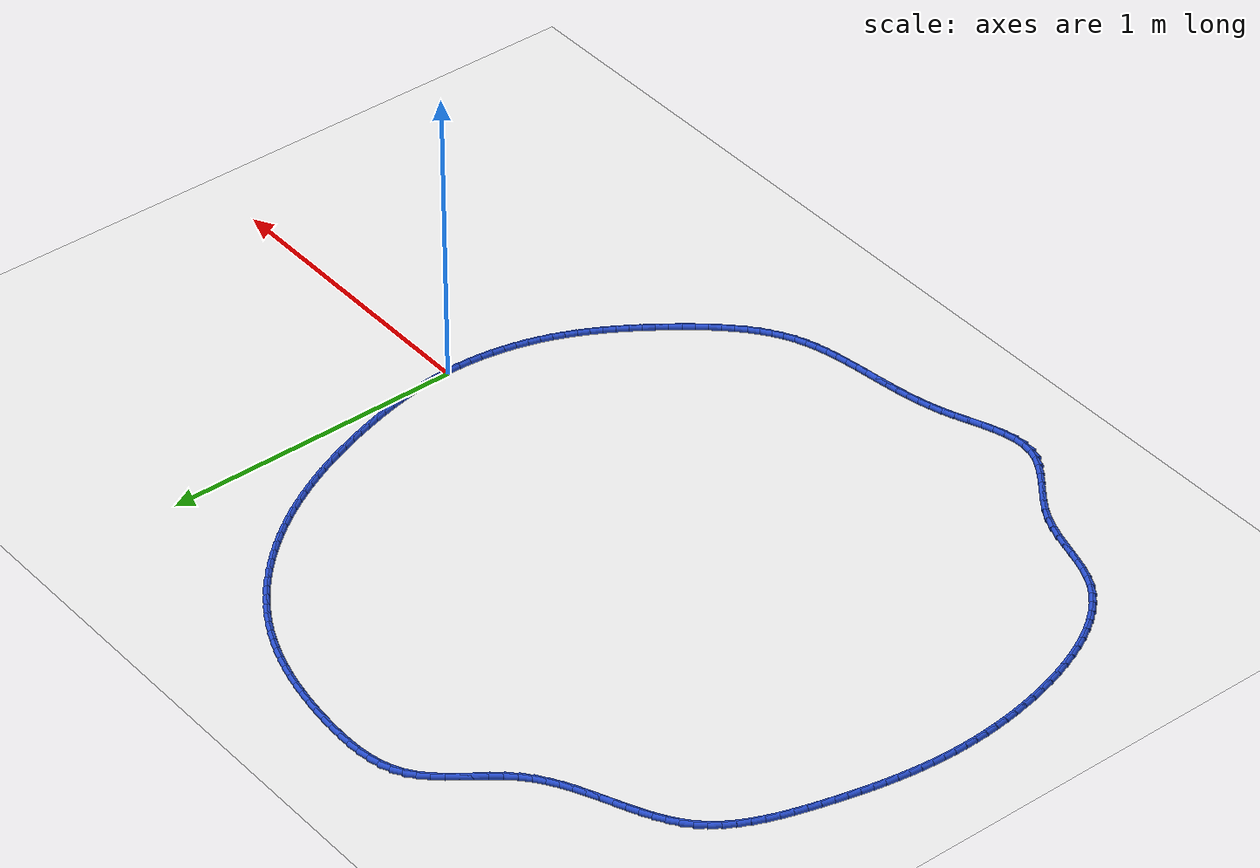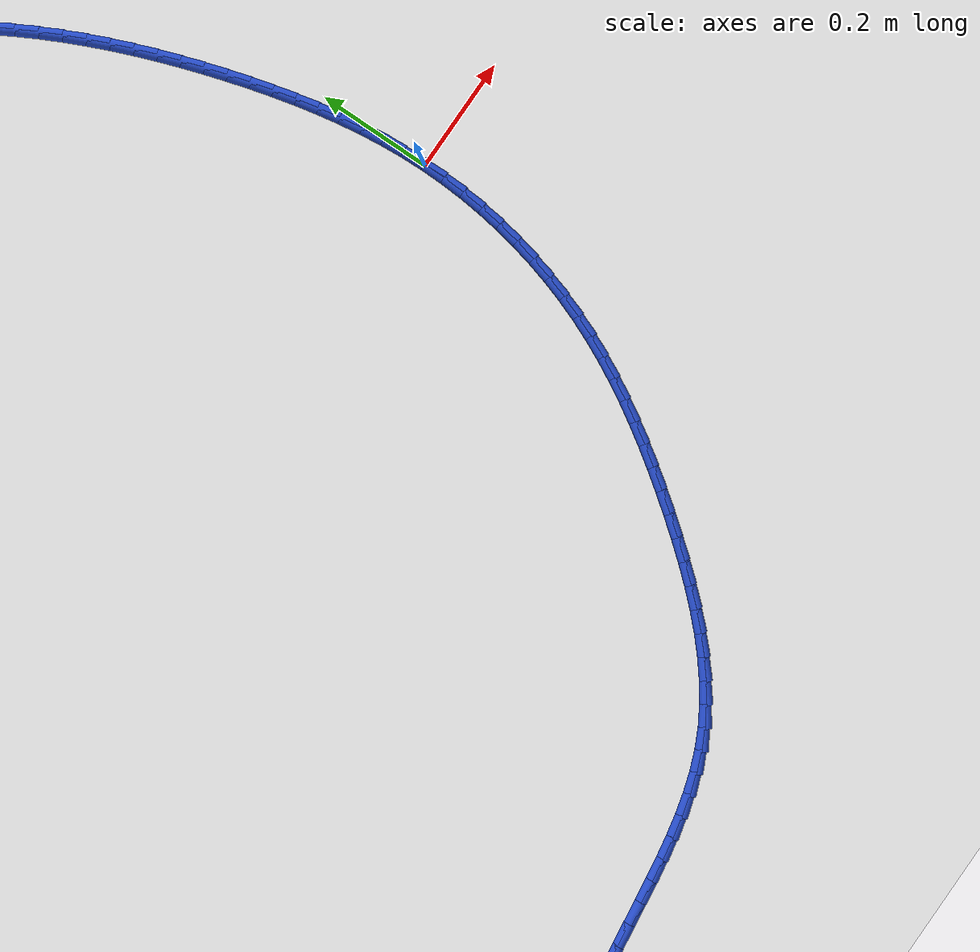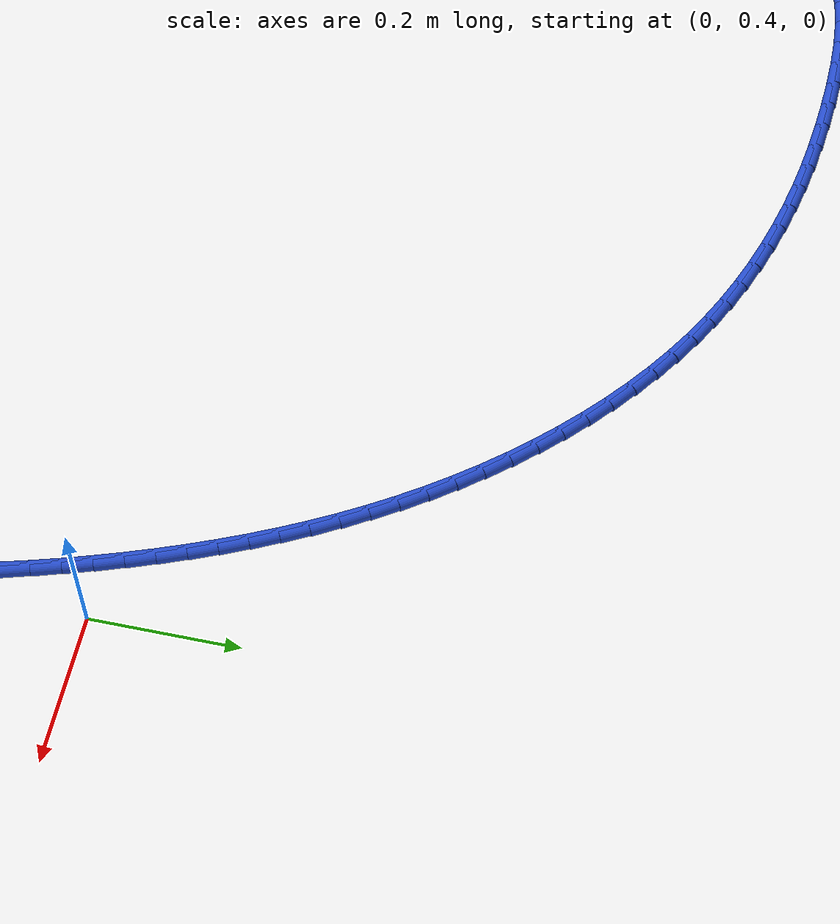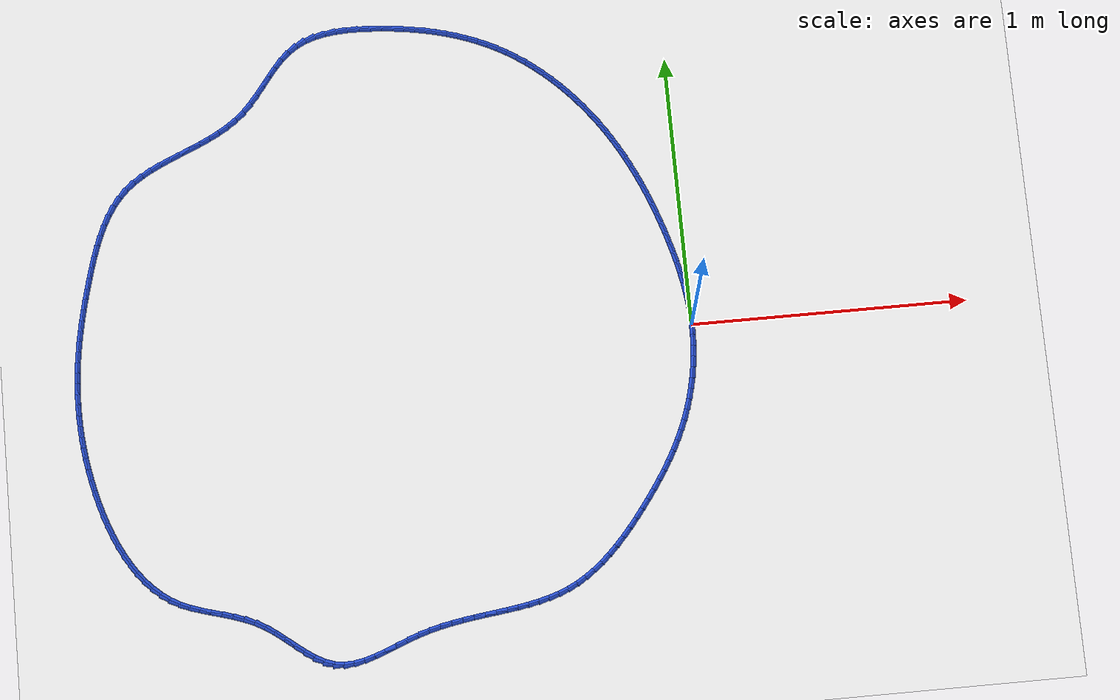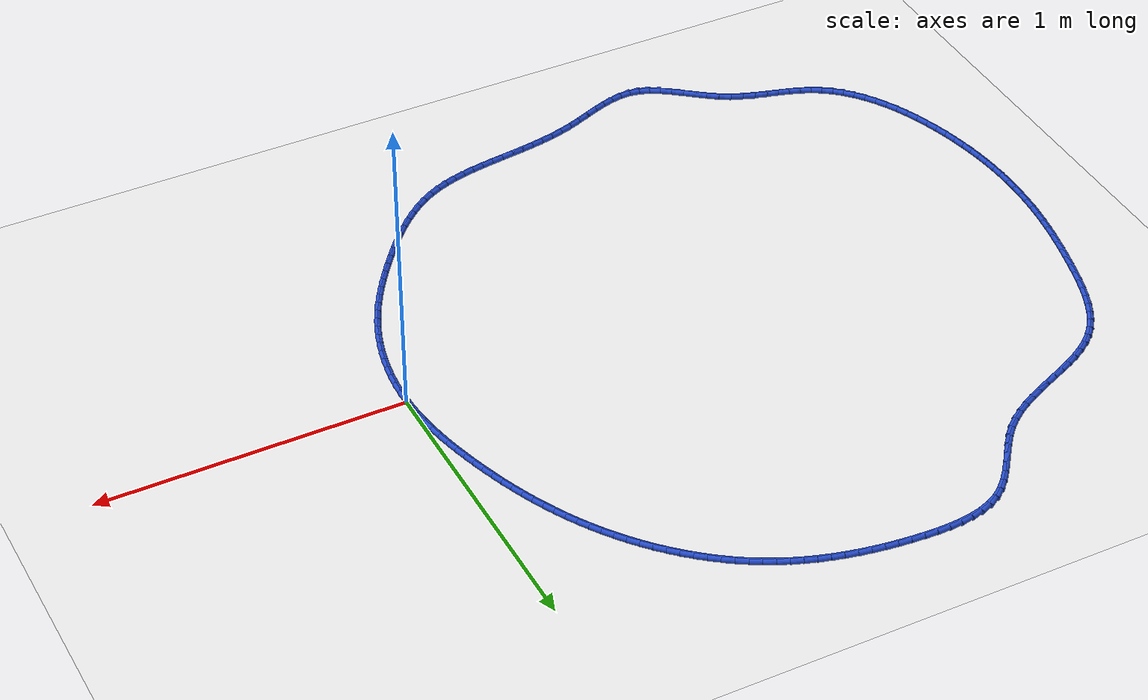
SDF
<sdf version="1.6">
 <world name="default">
  <light name="sun" type="directional">
   <pose>0 0 10 0 -0 0</pose>
   <diffuse>0.8 0.8 0.8 1</diffuse>
   <specular>0.2 0.2 0.2 1</specular>
   <attenuation>
    <range>1000</range>
    <constant>0.9</constant>
    <linear>0.01</linear>
    <quadratic>0.001</quadratic>
   </attenuation>
   <direction>-0.5 0.1 -0.9</direction>
  </light>
  <model name="ground_plane">
   <static>1</static>
   <link name="link">
    <collision name="collision">
     <geometry><plane><normal>0 0 1</normal><size>100 100</size></plane></geometry>
     <surface><friction><ode><mu>100</mu><mu2>50</mu2></ode></friction></surface>
    </collision>
    <visual name="visual">
     <cast_shadows>0</cast_shadows>
     <geometry><plane><normal>0 0 1</normal><size>100 100</size></plane></geometry>
     <material>
      <script><uri>file://media/materials/scripts/gazebo.material</uri><name>Gazebo/WhiteGlow</name></script>
     </material>
    </visual>
   </link>
  </model>
  <gravity>0 0 -9.8</gravity>
  <magnetic_field>6e-06 2.3e-05 -4.2e-05</magnetic_field>
  <atmosphere type="adiabatic"/>
  <physics name="default_physics" default="0" type="ode">
   <max_step_size>0.001</max_step_size>
   <real_time_factor>1</real_time_factor>
   <real_time_update_rate>1000</real_time_update_rate>
  </physics>
  <scene><ambient>0.4 0.4 0.4 1</ambient><background>0.7 0.7 0.7 1</background><shadows>1</shadows></scene>
  <spherical_coordinates>
   <surface_model>EARTH_WGS84</surface_model>
   <latitude_deg>0</latitude_deg>
   <longitude_deg>0</longitude_deg>
   <elevation>0</elevation>
   <heading_deg>0</heading_deg>
  </spherical_coordinates>
  <model name="line">
   <link name="link_0">
    <pose>-1.734723475976807e-18 6.938893903907228e-17 0.01 0 1.57 -1.5323101199211955</pose>
    <collision name="collision">
     <geometry><cylinder><radius>0.01</radius><length>0.08</length></cylinder></geometry>
    </collision>
    <visual name="visual">
     <material>
      <script><name>Gazebo/Blue</name><uri>file://media/materials/scripts/gazebo.material</uri></script>
     </material>
     <geometry><cylinder><radius>0.01</radius><length>0.08</length></cylinder></geometry>
    </visual>
   </link>
   <link name="link_1">
    <pose>-0.0015213970700239878 0.03951144996980983 0.01 0 1.57 -1.4903846976109987</pose>
    <collision name="collision">
     <geometry><cylinder><radius>0.01</radius><length>0.08</length></cylinder></geometry>
    </collision>
    <visual name="visual">
     <material>
      <script><name>Gazebo/Blue</name><uri>file://media/materials/scripts/gazebo.material</uri></script>
     </material>
     <geometry><cylinder><radius>0.01</radius><length>0.08</length></cylinder></geometry>
    </visual>
   </link>
   <link name="link_2">
    <pose>-0.00469291365753506 0.0788674232774882 0.01 0 1.57 -1.4515477809907944</pose>
    <collision name="collision">
     <geometry><cylinder><radius>0.01</radius><length>0.08</length></cylinder></geometry>
    </collision>
    <visual name="visual">
     <material>
      <script><name>Gazebo/Blue</name><uri>file://media/materials/scripts/gazebo.material</uri></script>
     </material>
     <geometry><cylinder><radius>0.01</radius><length>0.08</length></cylinder></geometry>
    </visual>
   </link>
   <link name="link_3">
    <pose>-0.009388990292405204 0.11806115709889219 0.01 0 1.57 -1.4158630483861034</pose>
    <collision name="collision">
     <geometry><cylinder><radius>0.01</radius><length>0.08</length></cylinder></geometry>
    </collision>
    <visual name="visual">
     <material>
      <script><name>Gazebo/Blue</name><uri>file://media/materials/scripts/gazebo.material</uri></script>
     </material>
     <geometry><cylinder><radius>0.01</radius><length>0.08</length></cylinder></geometry>
    </visual>
   </link>
   <link name="link_4">
    <pose>-0.015484067504506416 0.15708588860987882 0.01 0 1.57 -1.3833520352962583</pose>
    <collision name="collision">
     <geometry><cylinder><radius>0.01</radius><length>0.08</length></cylinder></geometry>
    </collision>
    <visual name="visual">
     <material>
      <script><name>Gazebo/Blue</name><uri>file://media/materials/scripts/gazebo.material</uri></script>
     </material>
     <geometry><cylinder><radius>0.01</radius><length>0.08</length></cylinder></geometry>
    </visual>
   </link>
   <link name="link_5">
    <pose>-0.02285258582371067 0.19593485498630508 0.01 0 1.57 -1.354004692443112</pose>
    <collision name="collision">
     <geometry><cylinder><radius>0.01</radius><length>0.08</length></cylinder></geometry>
    </collision>
    <visual name="visual">
     <material>
      <script><name>Gazebo/Blue</name><uri>file://media/materials/scripts/gazebo.material</uri></script>
     </material>
     <geometry><cylinder><radius>0.01</radius><length>0.08</length></cylinder></geometry>
    </visual>
   </link>
   <link name="link_6">
    <pose>-0.031368985779889946 0.2346012934040279 0.01 0 1.57 -1.327789300398814</pose>
    <collision name="collision">
     <geometry><cylinder><radius>0.01</radius><length>0.08</length></cylinder></geometry>
    </collision>
    <visual name="visual">
     <material>
      <script><name>Gazebo/Blue</name><uri>file://media/materials/scripts/gazebo.material</uri></script>
     </material>
     <geometry><cylinder><radius>0.01</radius><length>0.08</length></cylinder></geometry>
    </visual>
   </link>
   <link name="link_7">
    <pose>-0.040907707902916264 0.27307844103890444 0.01 0 1.57 -1.3046613184112068</pose>
    <collision name="collision">
     <geometry><cylinder><radius>0.01</radius><length>0.08</length></cylinder></geometry>
    </collision>
    <visual name="visual">
     <material>
      <script><name>Gazebo/Blue</name><uri>file://media/materials/scripts/gazebo.material</uri></script>
     </material>
     <geometry><cylinder><radius>0.01</radius><length>0.08</length></cylinder></geometry>
    </visual>
   </link>
   <link name="link_8">
    <pose>-0.05134319272266158 0.31135953506679165 0.01 0 1.57 -1.2845657536202524</pose>
    <collision name="collision">
     <geometry><cylinder><radius>0.01</radius><length>0.08</length></cylinder></geometry>
    </collision>
    <visual name="visual">
     <material>
      <script><name>Gazebo/Blue</name><uri>file://media/materials/scripts/gazebo.material</uri></script>
     </material>
     <geometry><cylinder><radius>0.01</radius><length>0.08</length></cylinder></geometry>
    </visual>
   </link>
   <link name="link_9">
    <pose>-0.06255008660807339 0.3494377753334058 0.01 0 1.57 -1.2662746298518537</pose>
    <collision name="collision">
     <geometry><cylinder><radius>0.01</radius><length>0.08</length></cylinder></geometry>
    </collision>
    <visual name="visual">
     <material>
      <script><name>Gazebo/Blue</name><uri>file://media/materials/scripts/gazebo.material</uri></script>
     </material>
     <geometry><cylinder><radius>0.01</radius><length>0.08</length></cylinder></geometry>
    </visual>
   </link>
   <link name="link_10">
    <pose>-0.0744494468587785 0.38729794478611923 0.01 0 1.57 -1.247087587731008</pose>
    <collision name="collision">
     <geometry><cylinder><radius>0.01</radius><length>0.08</length></cylinder></geometry>
    </collision>
    <visual name="visual">
     <material>
      <script><name>Gazebo/Blue</name><uri>file://media/materials/scripts/gazebo.material</uri></script>
     </material>
     <geometry><cylinder><radius>0.01</radius><length>0.08</length></cylinder></geometry>
    </visual>
   </link>
   <link name="link_11">
    <pose>-0.08706727581632619 0.42490579396470984 0.01 0 1.57 -1.22661730961343</pose>
    <collision name="collision">
     <geometry><cylinder><radius>0.01</radius><length>0.08</length></cylinder></geometry>
    </collision>
    <visual name="visual">
     <material>
      <script><name>Gazebo/Blue</name><uri>file://media/materials/scripts/gazebo.material</uri></script>
     </material>
     <geometry><cylinder><radius>0.01</radius><length>0.08</length></cylinder></geometry>
    </visual>
   </link>
   <link name="link_12">
    <pose>-0.10044399449879922 0.46222445849619886 0.01 0 1.57 -1.204845244103253</pose>
    <collision name="collision">
     <geometry><cylinder><radius>0.01</radius><length>0.08</length></cylinder></geometry>
    </collision>
    <visual name="visual">
     <material>
      <script><name>Gazebo/Blue</name><uri>file://media/materials/scripts/gazebo.material</uri></script>
     </material>
     <geometry><cylinder><radius>0.01</radius><length>0.08</length></cylinder></geometry>
    </visual>
   </link>
   <link name="link_13">
    <pose>-0.11462002392428056 0.4992170740076088 0.01 0 1.57 -1.1817555785301266</pose>
    <collision name="collision">
     <geometry><cylinder><radius>0.01</radius><length>0.08</length></cylinder></geometry>
    </collision>
    <visual name="visual">
     <material>
      <script><name>Gazebo/Blue</name><uri>file://media/materials/scripts/gazebo.material</uri></script>
     </material>
     <geometry><cylinder><radius>0.01</radius><length>0.08</length></cylinder></geometry>
    </visual>
   </link>
   <link name="link_14">
    <pose>-0.129635785110853 0.5358467761259611 0.01 0 1.57 -1.1573363844770337</pose>
    <collision name="collision">
     <geometry><cylinder><radius>0.01</radius><length>0.08</length></cylinder></geometry>
    </collision>
    <visual name="visual">
     <material>
      <script><name>Gazebo/Blue</name><uri>file://media/materials/scripts/gazebo.material</uri></script>
     </material>
     <geometry><cylinder><radius>0.01</radius><length>0.08</length></cylinder></geometry>
    </visual>
   </link>
   <link name="link_15">
    <pose>-0.14553169907659944 0.5720767004782777 0.01 0 1.57 -1.131580869920373</pose>
    <collision name="collision">
     <geometry><cylinder><radius>0.01</radius><length>0.08</length></cylinder></geometry>
    </collision>
    <visual name="visual">
     <material>
      <script><name>Gazebo/Blue</name><uri>file://media/materials/scripts/gazebo.material</uri></script>
     </material>
     <geometry><cylinder><radius>0.01</radius><length>0.08</length></cylinder></geometry>
    </visual>
   </link>
   <link name="link_16">
    <pose>-0.16234818683960264 0.6078699826915804 0.01 0 1.57 -1.10448872242798</pose>
    <collision name="collision">
     <geometry><cylinder><radius>0.01</radius><length>0.08</length></cylinder></geometry>
    </collision>
    <visual name="visual">
     <material>
      <script><name>Gazebo/Blue</name><uri>file://media/materials/scripts/gazebo.material</uri></script>
     </material>
     <geometry><cylinder><radius>0.01</radius><length>0.08</length></cylinder></geometry>
    </visual>
   </link>
   <link name="link_17">
    <pose>-0.18012566941794556 0.6431897583928912 0.01 0 1.57 -1.076067516809016</pose>
    <collision name="collision">
     <geometry><cylinder><radius>0.01</radius><length>0.08</length></cylinder></geometry>
    </collision>
    <visual name="visual">
     <material>
      <script><name>Gazebo/Blue</name><uri>file://media/materials/scripts/gazebo.material</uri></script>
     </material>
     <geometry><cylinder><radius>0.01</radius><length>0.08</length></cylinder></geometry>
    </visual>
   </link>
   <link name="link_18">
    <pose>-0.1989045678297111 0.6779991632092321 0.01 0 1.57 -1.046334147807426</pose>
    <collision name="collision">
     <geometry><cylinder><radius>0.01</radius><length>0.08</length></cylinder></geometry>
    </collision>
    <visual name="visual">
     <material>
      <script><name>Gazebo/Blue</name><uri>file://media/materials/scripts/gazebo.material</uri></script>
     </material>
     <geometry><cylinder><radius>0.01</radius><length>0.08</length></cylinder></geometry>
    </visual>
   </link>
   <link name="link_19">
    <pose>-0.21872530309298194 0.7122613327676243 0.01 0 1.57 -1.0153162345164217</pose>
    <collision name="collision">
     <geometry><cylinder><radius>0.01</radius><length>0.08</length></cylinder></geometry>
    </collision>
    <visual name="visual">
     <material>
      <script><name>Gazebo/Blue</name><uri>file://media/materials/scripts/gazebo.material</uri></script>
     </material>
     <geometry><cylinder><radius>0.01</radius><length>0.08</length></cylinder></geometry>
    </visual>
   </link>
   <link name="link_20">
    <pose>-0.23962829622584125 0.7459394026950906 0.01 0 1.57 -0.9830534292479374</pose>
    <collision name="collision">
     <geometry><cylinder><radius>0.01</radius><length>0.08</length></cylinder></geometry>
    </collision>
    <visual name="visual">
     <material>
      <script><name>Gazebo/Blue</name><uri>file://media/materials/scripts/gazebo.material</uri></script>
     </material>
     <geometry><cylinder><radius>0.01</radius><length>0.08</length></cylinder></geometry>
    </visual>
   </link>
   <link name="link_21">
    <pose>-0.26165396824637155 0.778996508618652 0.01 0 1.57 -0.9496252607574956</pose>
    <collision name="collision">
     <geometry><cylinder><radius>0.01</radius><length>0.08</length></cylinder></geometry>
    </collision>
    <visual name="visual">
     <material>
      <script><name>Gazebo/Blue</name><uri>file://media/materials/scripts/gazebo.material</uri></script>
     </material>
     <geometry><cylinder><radius>0.01</radius><length>0.08</length></cylinder></geometry>
    </visual>
   </link>
   <link name="link_22">
    <pose>-0.2848399504521031 0.8113937166809627 0.01 0 1.57 -0.9154435720531728</pose>
    <collision name="collision">
     <geometry><cylinder><radius>0.01</radius><length>0.08</length></cylinder></geometry>
    </collision>
    <visual name="visual">
     <material>
      <script><name>Gazebo/Blue</name><uri>file://media/materials/scripts/gazebo.material</uri></script>
     </material>
     <geometry><cylinder><radius>0.01</radius><length>0.08</length></cylinder></geometry>
    </visual>
   </link>
   <link name="link_23">
    <pose>-0.30918233513115206 0.8430612783502249 0.01 0 1.57 -0.8806823990476138</pose>
    <collision name="collision">
     <geometry><cylinder><radius>0.01</radius><length>0.08</length></cylinder></geometry>
    </collision>
    <visual name="visual">
     <material>
      <script><name>Gazebo/Blue</name><uri>file://media/materials/scripts/gazebo.material</uri></script>
     </material>
     <geometry><cylinder><radius>0.01</radius><length>0.08</length></cylinder></geometry>
    </visual>
   </link>
   <link name="link_24">
    <pose>-0.33464534150881653 0.8739058008607417 0.01 0 1.57 -0.8451848546975982</pose>
    <collision name="collision">
     <geometry><cylinder><radius>0.01</radius><length>0.08</length></cylinder></geometry>
    </collision>
    <visual name="visual">
     <material>
      <script><name>Gazebo/Blue</name><uri>file://media/materials/scripts/gazebo.material</uri></script>
     </material>
     <geometry><cylinder><radius>0.01</radius><length>0.08</length></cylinder></geometry>
    </visual>
   </link>
   <link name="link_25">
    <pose>-0.36119237489483563 0.9038332876639299 0.01 0 1.57 -0.8087874085351197</pose>
    <collision name="collision">
     <geometry><cylinder><radius>0.01</radius><length>0.08</length></cylinder></geometry>
    </collision>
    <visual name="visual">
     <material>
      <script><name>Gazebo/Blue</name><uri>file://media/materials/scripts/gazebo.material</uri></script>
     </material>
     <geometry><cylinder><radius>0.01</radius><length>0.08</length></cylinder></geometry>
    </visual>
   </link>
   <link name="link_26">
    <pose>-0.388786840598948 0.9327497422112065 0.01 0 1.57 -0.7713274221592068</pose>
    <collision name="collision">
     <geometry><cylinder><radius>0.01</radius><length>0.08</length></cylinder></geometry>
    </collision>
    <visual name="visual">
     <material>
      <script><name>Gazebo/Blue</name><uri>file://media/materials/scripts/gazebo.material</uri></script>
     </material>
     <geometry><cylinder><radius>0.01</radius><length>0.08</length></cylinder></geometry>
    </visual>
   </link>
   <link name="link_27">
    <pose>-0.4173921439308921 0.9605611679539883 0.01 0 1.57 -0.7326434012178132</pose>
    <collision name="collision">
     <geometry><cylinder><radius>0.01</radius><length>0.08</length></cylinder></geometry>
    </collision>
    <visual name="visual">
     <material>
      <script><name>Gazebo/Blue</name><uri>file://media/materials/scripts/gazebo.material</uri></script>
     </material>
     <geometry><cylinder><radius>0.01</radius><length>0.08</length></cylinder></geometry>
    </visual>
   </link>
   <link name="link_28">
    <pose>-0.44697169020040695 0.9871735683436921 0.01 0 1.57 -0.6925758593957346</pose>
    <collision name="collision">
     <geometry><cylinder><radius>0.01</radius><length>0.08</length></cylinder></geometry>
    </collision>
    <visual name="visual">
     <material>
      <script><name>Gazebo/Blue</name><uri>file://media/materials/scripts/gazebo.material</uri></script>
     </material>
     <geometry><cylinder><radius>0.01</radius><length>0.08</length></cylinder></geometry>
    </visual>
   </link>
   <link name="link_29">
    <pose>-0.47748888471723117 1.0124929468317347 0.01 0 1.57 -0.6509689164352124</pose>
    <collision name="collision">
     <geometry><cylinder><radius>0.01</radius><length>0.08</length></cylinder></geometry>
    </collision>
    <visual name="visual">
     <material>
      <script><name>Gazebo/Blue</name><uri>file://media/materials/scripts/gazebo.material</uri></script>
     </material>
     <geometry><cylinder><radius>0.01</radius><length>0.08</length></cylinder></geometry>
    </visual>
   </link>
   <link name="link_30">
    <pose>-0.5089071327911037 1.0364253068695335 0.01 0 1.57 -0.6076727666682773</pose>
    <collision name="collision">
     <geometry><cylinder><radius>0.01</radius><length>0.08</length></cylinder></geometry>
    </collision>
    <visual name="visual">
     <material>
      <script><name>Gazebo/Blue</name><uri>file://media/materials/scripts/gazebo.material</uri></script>
     </material>
     <geometry><cylinder><radius>0.01</radius><length>0.08</length></cylinder></geometry>
    </visual>
   </link>
   <link name="link_31">
    <pose>-0.5411898397317629 1.0588766519085047 0.01 0 1.57 -0.5625471573862791</pose>
    <collision name="collision">
     <geometry><cylinder><radius>0.01</radius><length>0.08</length></cylinder></geometry>
    </collision>
    <visual name="visual">
     <material>
      <script><name>Gazebo/Blue</name><uri>file://media/materials/scripts/gazebo.material</uri></script>
     </material>
     <geometry><cylinder><radius>0.01</radius><length>0.08</length></cylinder></geometry>
    </visual>
   </link>
   <link name="link_32">
    <pose>-0.574300410848948 1.0797529854000656 0.01 0 1.57 -0.5158658099053233</pose>
    <collision name="collision">
     <geometry><cylinder><radius>0.01</radius><length>0.08</length></cylinder></geometry>
    </collision>
    <visual name="visual">
     <material>
      <script><name>Gazebo/Blue</name><uri>file://media/materials/scripts/gazebo.material</uri></script>
     </material>
     <geometry><cylinder><radius>0.01</radius><length>0.08</length></cylinder></geometry>
    </visual>
   </link>
   <link name="link_33">
    <pose>-0.6082041989019451 1.098979324305914 0.01 0 1.57 -0.46965449911761487</pose>
    <collision name="collision">
     <geometry><cylinder><radius>0.01</radius><length>0.08</length></cylinder></geometry>
    </collision>
    <visual name="visual">
     <material>
      <script><name>Gazebo/Blue</name><uri>file://media/materials/scripts/gazebo.material</uri></script>
     </material>
     <geometry><cylinder><radius>0.01</radius><length>0.08</length></cylinder></geometry>
    </visual>
   </link>
   <link name="link_34">
    <pose>-0.6428763744331981 1.1165765394296092 0.01 0 1.57 -0.4247454569267067</pose>
    <collision name="collision">
     <geometry><cylinder><radius>0.01</radius><length>0.08</length></cylinder></geometry>
    </collision>
    <visual name="visual">
     <material>
      <script><name>Gazebo/Blue</name><uri>file://media/materials/scripts/gazebo.material</uri></script>
     </material>
     <geometry><cylinder><radius>0.01</radius><length>0.08</length></cylinder></geometry>
    </visual>
   </link>
   <link name="link_35">
    <pose>-0.6782951948777229 1.1325956397950916 0.01 0 1.57 -0.381329352784515</pose>
    <collision name="collision">
     <geometry><cylinder><radius>0.01</radius><length>0.08</length></cylinder></geometry>
    </collision>
    <visual name="visual">
     <material>
      <script><name>Gazebo/Blue</name><uri>file://media/materials/scripts/gazebo.material</uri></script>
     </material>
     <geometry><cylinder><radius>0.01</radius><length>0.08</length></cylinder></geometry>
    </visual>
   </link>
   <link name="link_36">
    <pose>-0.7144389187947567 1.1470876454024044 0.01 0 1.57 -0.33956161476217556</pose>
    <collision name="collision">
     <geometry><cylinder><radius>0.01</radius><length>0.08</length></cylinder></geometry>
    </collision>
    <visual name="visual">
     <material>
      <script><name>Gazebo/Blue</name><uri>file://media/materials/scripts/gazebo.material</uri></script>
     </material>
     <geometry><cylinder><radius>0.01</radius><length>0.08</length></cylinder></geometry>
    </visual>
   </link>
   <link name="link_37">
    <pose>-0.7512858047435373 1.1601035762515906 0.01 0 1.57 -0.29956244585359215</pose>
    <collision name="collision">
     <geometry><cylinder><radius>0.01</radius><length>0.08</length></cylinder></geometry>
    </collision>
    <visual name="visual">
     <material>
      <script><name>Gazebo/Blue</name><uri>file://media/materials/scripts/gazebo.material</uri></script>
     </material>
     <geometry><cylinder><radius>0.01</radius><length>0.08</length></cylinder></geometry>
    </visual>
   </link>
   <link name="link_38">
    <pose>-0.7888141112833023 1.1716944523426926 0.01 0 1.57 -0.2614182425018095</pose>
    <collision name="collision">
     <geometry><cylinder><radius>0.01</radius><length>0.08</length></cylinder></geometry>
    </collision>
    <visual name="visual">
     <material>
      <script><name>Gazebo/Blue</name><uri>file://media/materials/scripts/gazebo.material</uri></script>
     </material>
     <geometry><cylinder><radius>0.01</radius><length>0.08</length></cylinder></geometry>
    </visual>
   </link>
   <link name="link_39">
    <pose>-0.8270020969732892 1.1819112936757543 0.01 0 1.57 -0.22518425615902832</pose>
    <collision name="collision">
     <geometry><cylinder><radius>0.01</radius><length>0.08</length></cylinder></geometry>
    </collision>
    <visual name="visual">
     <material>
      <script><name>Gazebo/Blue</name><uri>file://media/materials/scripts/gazebo.material</uri></script>
     </material>
     <geometry><cylinder><radius>0.01</radius><length>0.08</length></cylinder></geometry>
    </visual>
   </link>
   <link name="link_40">
    <pose>-0.865828020372736 1.1908051202508183 0.01 0 1.57 -0.19088808559010412</pose>
    <collision name="collision">
     <geometry><cylinder><radius>0.01</radius><length>0.08</length></cylinder></geometry>
    </collision>
    <visual name="visual">
     <material>
      <script><name>Gazebo/Blue</name><uri>file://media/materials/scripts/gazebo.material</uri></script>
     </material>
     <geometry><cylinder><radius>0.01</radius><length>0.08</length></cylinder></geometry>
    </visual>
   </link>
   <link name="link_41">
    <pose>-0.9052701400408796 1.1984269520679274 0.01 0 1.57 -0.15853361645858974</pose>
    <collision name="collision">
     <geometry><cylinder><radius>0.01</radius><length>0.08</length></cylinder></geometry>
    </collision>
    <visual name="visual">
     <material>
      <script><name>Gazebo/Blue</name><uri>file://media/materials/scripts/gazebo.material</uri></script>
     </material>
     <geometry><cylinder><radius>0.01</radius><length>0.08</length></cylinder></geometry>
    </visual>
   </link>
   <link name="link_42">
    <pose>-0.9453067145369582 1.2048278091271252 0.01 0 1.57 -0.12810508604536114</pose>
    <collision name="collision">
     <geometry><cylinder><radius>0.01</radius><length>0.08</length></cylinder></geometry>
    </collision>
    <visual name="visual">
     <material>
      <script><name>Gazebo/Blue</name><uri>file://media/materials/scripts/gazebo.material</uri></script>
     </material>
     <geometry><cylinder><radius>0.01</radius><length>0.08</length></cylinder></geometry>
    </visual>
   </link>
   <link name="link_43">
    <pose>-0.9859160024202094 1.210058711428454 0.01 0 1.57 -0.0995710268657054</pose>
    <collision name="collision">
     <geometry><cylinder><radius>0.01</radius><length>0.08</length></cylinder></geometry>
    </collision>
    <visual name="visual">
     <material>
      <script><name>Gazebo/Blue</name><uri>file://media/materials/scripts/gazebo.material</uri></script>
     </material>
     <geometry><cylinder><radius>0.01</radius><length>0.08</length></cylinder></geometry>
    </visual>
   </link>
   <link name="link_44">
    <pose>-1.0270762622498706 1.214170678971957 0.01 0 1.57 -0.0727830464954815</pose>
    <collision name="collision">
     <geometry><cylinder><radius>0.01</radius><length>0.08</length></cylinder></geometry>
    </collision>
    <visual name="visual">
     <material>
      <script><name>Gazebo/Blue</name><uri>file://media/materials/scripts/gazebo.material</uri></script>
     </material>
     <geometry><cylinder><radius>0.01</radius><length>0.08</length></cylinder></geometry>
    </visual>
   </link>
   <link name="link_45">
    <pose>-1.0687619582253773 1.217210059726688 0.01 0 1.57 -0.04250375442364984</pose>
    <collision name="collision">
     <geometry><cylinder><radius>0.01</radius><length>0.08</length></cylinder></geometry>
    </collision>
    <visual name="visual">
     <material>
      <script><name>Gazebo/Blue</name><uri>file://media/materials/scripts/gazebo.material</uri></script>
     </material>
     <geometry><cylinder><radius>0.01</radius><length>0.08</length></cylinder></geometry>
    </visual>
   </link>
   <link name="link_46">
    <pose>-1.1107633193106083 1.2189963510795672 0.01 0 1.57 -0.0006882578097971925</pose>
    <collision name="collision">
     <geometry><cylinder><radius>0.01</radius><length>0.08</length></cylinder></geometry>
    </collision>
    <visual name="visual">
     <material>
      <script><name>Gazebo/Blue</name><uri>file://media/materials/scripts/gazebo.material</uri></script>
     </material>
     <geometry><cylinder><radius>0.01</radius><length>0.08</length></cylinder></geometry>
    </visual>
   </link>
   <link name="link_47">
    <pose>-1.152607521391394 1.2190251506829914 0.01 0 1.57 0.05475779179109832</pose>
    <collision name="collision">
     <geometry><cylinder><radius>0.01</radius><length>0.08</length></cylinder></geometry>
    </collision>
    <visual name="visual">
     <material>
      <script><name>Gazebo/Blue</name><uri>file://media/materials/scripts/gazebo.material</uri></script>
     </material>
     <geometry><cylinder><radius>0.01</radius><length>0.08</length></cylinder></geometry>
    </visual>
   </link>
   <link name="link_48">
    <pose>-1.1938015529659616 1.2167671992687163 0.01 0 1.57 0.1260166704637612</pose>
    <collision name="collision">
     <geometry><cylinder><radius>0.01</radius><length>0.08</length></cylinder></geometry>
    </collision>
    <visual name="visual">
     <material>
      <script><name>Gazebo/Blue</name><uri>file://media/materials/scripts/gazebo.material</uri></script>
     </material>
     <geometry><cylinder><radius>0.01</radius><length>0.08</length></cylinder></geometry>
    </visual>
   </link>
   <link name="link_49">
    <pose>-1.2338524025325377 1.2116932375684957 0.01 0 1.57 0.2157557794045252</pose>
    <collision name="collision">
     <geometry><cylinder><radius>0.01</radius><length>0.08</length></cylinder></geometry>
    </collision>
    <visual name="visual">
     <material>
      <script><name>Gazebo/Blue</name><uri>file://media/materials/scripts/gazebo.material</uri></script>
     </material>
     <geometry><cylinder><radius>0.01</radius><length>0.08</length></cylinder></geometry>
    </visual>
   </link>
   <link name="link_50">
    <pose>-1.2722670585893485 1.2032740063140848 0.01 0 1.57 0.3266686214591587</pose>
    <collision name="collision">
     <geometry><cylinder><radius>0.01</radius><length>0.08</length></cylinder></geometry>
    </collision>
    <visual name="visual">
     <material>
      <script><name>Gazebo/Blue</name><uri>file://media/materials/scripts/gazebo.material</uri></script>
     </material>
     <geometry><cylinder><radius>0.01</radius><length>0.08</length></cylinder></geometry>
    </visual>
   </link>
   <link name="link_51">
    <pose>-1.308552509634621 1.1909802462372376 0.01 0 1.57 0.46045641087052736</pose>
    <collision name="collision">
     <geometry><cylinder><radius>0.01</radius><length>0.08</length></cylinder></geometry>
    </collision>
    <visual name="visual">
     <material>
      <script><name>Gazebo/Blue</name><uri>file://media/materials/scripts/gazebo.material</uri></script>
     </material>
     <geometry><cylinder><radius>0.01</radius><length>0.08</length></cylinder></geometry>
    </visual>
   </link>
   <link name="link_52">
    <pose>-1.3422157441665823 1.1742826980697096 0.01 0 1.57 0.6123308966010632</pose>
    <collision name="collision">
     <geometry><cylinder><radius>0.01</radius><length>0.08</length></cylinder></geometry>
    </collision>
    <visual name="visual">
     <material>
      <script><name>Gazebo/Blue</name><uri>file://media/materials/scripts/gazebo.material</uri></script>
     </material>
     <geometry><cylinder><radius>0.01</radius><length>0.08</length></cylinder></geometry>
    </visual>
   </link>
   <link name="link_53">
    <pose>-1.372851365841772 1.1527644199736857 0.01 0 1.57 0.7450191394744613</pose>
    <collision name="collision">
     <geometry><cylinder><radius>0.01</radius><length>0.08</length></cylinder></geometry>
    </collision>
    <visual name="visual">
     <material>
      <script><name>Gazebo/Blue</name><uri>file://media/materials/scripts/gazebo.material</uri></script>
     </material>
     <geometry><cylinder><radius>0.01</radius><length>0.08</length></cylinder></geometry>
    </visual>
   </link>
   <link name="link_54">
    <pose>-1.400809785552202 1.1269773701079138 0.01 0 1.57 0.839694833907889</pose>
    <collision name="collision">
     <geometry><cylinder><radius>0.01</radius><length>0.08</length></cylinder></geometry>
    </collision>
    <visual name="visual">
     <material>
      <script><name>Gazebo/Blue</name><uri>file://media/materials/scripts/gazebo.material</uri></script>
     </material>
     <geometry><cylinder><radius>0.01</radius><length>0.08</length></cylinder></geometry>
    </visual>
   </link>
   <link name="link_55">
    <pose>-1.4268277237244253 1.09796873251563 0.01 0 1.57 0.8985235812538525</pose>
    <collision name="collision">
     <geometry><cylinder><radius>0.01</radius><length>0.08</length></cylinder></geometry>
    </collision>
    <visual name="visual">
     <material>
      <script><name>Gazebo/Blue</name><uri>file://media/materials/scripts/gazebo.material</uri></script>
     </material>
     <geometry><cylinder><radius>0.01</radius><length>0.08</length></cylinder></geometry>
    </visual>
   </link>
   <link name="link_56">
    <pose>-1.451645009323115 1.0667896762013591 0.01 0 1.57 0.9246702709367717</pose>
    <collision name="collision">
     <geometry><cylinder><radius>0.01</radius><length>0.08</length></cylinder></geometry>
    </collision>
    <visual name="visual">
     <material>
      <script><name>Gazebo/Blue</name><uri>file://media/materials/scripts/gazebo.material</uri></script>
     </material>
     <geometry><cylinder><radius>0.01</radius><length>0.08</length></cylinder></geometry>
    </visual>
   </link>
   <link name="link_57">
    <pose>-1.4760014713129466 1.0344913701696272 0.01 0 1.57 0.9202013933354828</pose>
    <collision name="collision">
     <geometry><cylinder><radius>0.01</radius><length>0.08</length></cylinder></geometry>
    </collision>
    <visual name="visual">
     <material>
      <script><name>Gazebo/Blue</name><uri>file://media/materials/scripts/gazebo.material</uri></script>
     </material>
     <geometry><cylinder><radius>0.01</radius><length>0.08</length></cylinder></geometry>
    </visual>
   </link>
   <link name="link_58">
    <pose>-1.5006369386585932 1.0021249834249577 0.01 0 1.57 0.8855048744629658</pose>
    <collision name="collision">
     <geometry><cylinder><radius>0.01</radius><length>0.08</length></cylinder></geometry>
    </collision>
    <visual name="visual">
     <material>
      <script><name>Gazebo/Blue</name><uri>file://media/materials/scripts/gazebo.material</uri></script>
     </material>
     <geometry><cylinder><radius>0.01</radius><length>0.08</length></cylinder></geometry>
    </visual>
   </link>
   <link name="link_59">
    <pose>-1.5262912403247286 0.970741684971877 0.01 0 1.57 0.8194936094720184</pose>
    <collision name="collision">
     <geometry><cylinder><radius>0.01</radius><length>0.08</length></cylinder></geometry>
    </collision>
    <visual name="visual">
     <material>
      <script><name>Gazebo/Blue</name><uri>file://media/materials/scripts/gazebo.material</uri></script>
     </material>
     <geometry><cylinder><radius>0.01</radius><length>0.08</length></cylinder></geometry>
    </visual>
   </link>
   <link name="link_60">
    <pose>-1.5537042052760281 0.9413926438149092 0.01 0 1.57 0.7238740337518047</pose>
    <collision name="collision">
     <geometry><cylinder><radius>0.01</radius><length>0.08</length></cylinder></geometry>
    </collision>
    <visual name="visual">
     <material>
      <script><name>Gazebo/Blue</name><uri>file://media/materials/scripts/gazebo.material</uri></script>
     </material>
     <geometry><cylinder><radius>0.01</radius><length>0.08</length></cylinder></geometry>
    </visual>
   </link>
   <link name="link_61">
    <pose>-1.5835355423311497 0.9150233697677967 0.01 0 1.57 0.6284043990264641</pose>
    <collision name="collision">
     <geometry><cylinder><radius>0.01</radius><length>0.08</length></cylinder></geometry>
    </collision>
    <visual name="visual">
     <material>
      <script><name>Gazebo/Blue</name><uri>file://media/materials/scripts/gazebo.material</uri></script>
     </material>
     <geometry><cylinder><radius>0.01</radius><length>0.08</length></cylinder></geometry>
    </visual>
   </link>
   <link name="link_62">
    <pose>-1.6157260844606876 0.8916313484062057 0.01 0 1.57 0.5500857171411326</pose>
    <collision name="collision">
     <geometry><cylinder><radius>0.01</radius><length>0.08</length></cylinder></geometry>
    </collision>
    <visual name="visual">
     <material>
      <script><name>Gazebo/Blue</name><uri>file://media/materials/scripts/gazebo.material</uri></script>
     </material>
     <geometry><cylinder><radius>0.01</radius><length>0.08</length></cylinder></geometry>
    </visual>
   </link>
   <link name="link_63">
    <pose>-1.6498371894688357 0.8707136288862686 0.01 0 1.57 0.48929570230507824</pose>
    <collision name="collision">
     <geometry><cylinder><radius>0.01</radius><length>0.08</length></cylinder></geometry>
    </collision>
    <visual name="visual">
     <material>
      <script><name>Gazebo/Blue</name><uri>file://media/materials/scripts/gazebo.material</uri></script>
     </material>
     <geometry><cylinder><radius>0.01</radius><length>0.08</length></cylinder></geometry>
    </visual>
   </link>
   <link name="link_64">
    <pose>-1.6854267896014508 0.8517627428770731 0.01 0 1.57 0.4455437781821746</pose>
    <collision name="collision">
     <geometry><cylinder><radius>0.01</radius><length>0.08</length></cylinder></geometry>
    </collision>
    <visual name="visual">
     <material>
      <script><name>Gazebo/Blue</name><uri>file://media/materials/scripts/gazebo.material</uri></script>
     </material>
     <geometry><cylinder><radius>0.01</radius><length>0.08</length></cylinder></geometry>
    </visual>
   </link>
   <link name="link_65">
    <pose>-1.7220528171043918 0.8342712220477062 0.01 0 1.57 0.4181621753952915</pose>
    <collision name="collision">
     <geometry><cylinder><radius>0.01</radius><length>0.08</length></cylinder></geometry>
    </collision>
    <visual name="visual">
     <material>
      <script><name>Gazebo/Blue</name><uri>file://media/materials/scripts/gazebo.material</uri></script>
     </material>
     <geometry><cylinder><radius>0.01</radius><length>0.08</length></cylinder></geometry>
    </visual>
   </link>
   <link name="link_66">
    <pose>-1.7592732042235164 0.8177315980672555 0.01 0 1.57 0.4066611981520749</pose>
    <collision name="collision">
     <geometry><cylinder><radius>0.01</radius><length>0.08</length></cylinder></geometry>
    </collision>
    <visual name="visual">
     <material>
      <script><name>Gazebo/Blue</name><uri>file://media/materials/scripts/gazebo.material</uri></script>
     </material>
     <geometry><cylinder><radius>0.01</radius><length>0.08</length></cylinder></geometry>
    </visual>
   </link>
   <link name="link_67">
    <pose>-1.7966458832046823 0.8016364026048081 0.01 0 1.57 0.4109261468087719</pose>
    <collision name="collision">
     <geometry><cylinder><radius>0.01</radius><length>0.08</length></cylinder></geometry>
    </collision>
    <visual name="visual">
     <material>
      <script><name>Gazebo/Blue</name><uri>file://media/materials/scripts/gazebo.material</uri></script>
     </material>
     <geometry><cylinder><radius>0.01</radius><length>0.08</length></cylinder></geometry>
    </visual>
   </link>
   <link name="link_68">
    <pose>-1.833728786293748 0.7854781673294514 0.01 0 1.57 0.4313034782444437</pose>
    <collision name="collision">
     <geometry><cylinder><radius>0.01</radius><length>0.08</length></cylinder></geometry>
    </collision>
    <visual name="visual">
     <material>
      <script><name>Gazebo/Blue</name><uri>file://media/materials/scripts/gazebo.material</uri></script>
     </material>
     <geometry><cylinder><radius>0.01</radius><length>0.08</length></cylinder></geometry>
    </visual>
   </link>
   <link name="link_69">
    <pose>-1.8700798457365708 0.7687494239102722 0.01 0 1.57 0.46859637438087237</pose>
    <collision name="collision">
     <geometry><cylinder><radius>0.01</radius><length>0.08</length></cylinder></geometry>
    </collision>
    <visual name="visual">
     <material>
      <script><name>Gazebo/Blue</name><uri>file://media/materials/scripts/gazebo.material</uri></script>
     </material>
     <geometry><cylinder><radius>0.01</radius><length>0.08</length></cylinder></geometry>
    </visual>
   </link>
   <link name="link_70">
    <pose>-1.9052569937790094 0.7509427040163587 0.01 0 1.57 0.5239476533895783</pose>
    <collision name="collision">
     <geometry><cylinder><radius>0.01</radius><length>0.08</length></cylinder></geometry>
    </collision>
    <visual name="visual">
     <material>
      <script><name>Gazebo/Blue</name><uri>file://media/materials/scripts/gazebo.material</uri></script>
     </material>
     <geometry><cylinder><radius>0.01</radius><length>0.08</length></cylinder></geometry>
    </visual>
   </link>
   <link name="link_71">
    <pose>-1.9388181626669212 0.7315505393167971 0.01 0 1.57 0.5985418888384493</pose>
    <collision name="collision">
     <geometry><cylinder><radius>0.01</radius><length>0.08</length></cylinder></geometry>
    </collision>
    <visual name="visual">
     <material>
      <script><name>Gazebo/Blue</name><uri>file://media/materials/scripts/gazebo.material</uri></script>
     </material>
     <geometry><cylinder><radius>0.01</radius><length>0.08</length></cylinder></geometry>
    </visual>
   </link>
   <link name="link_72">
    <pose>-1.9703212846461642 0.7100654614806758 0.01 0 1.57 0.6930324238551998</pose>
    <collision name="collision">
     <geometry><cylinder><radius>0.01</radius><length>0.08</length></cylinder></geometry>
    </collision>
    <visual name="visual">
     <material>
      <script><name>Gazebo/Blue</name><uri>file://media/materials/scripts/gazebo.material</uri></script>
     </material>
     <geometry><cylinder><radius>0.01</radius><length>0.08</length></cylinder></geometry>
    </visual>
   </link>
   <link name="link_73">
    <pose>-1.9993242919625964 0.6859800021770815 0.01 0 1.57 0.8052334358060059</pose>
    <collision name="collision">
     <geometry><cylinder><radius>0.01</radius><length>0.08</length></cylinder></geometry>
    </collision>
    <visual name="visual">
     <material>
      <script><name>Gazebo/Blue</name><uri>file://media/materials/scripts/gazebo.material</uri></script>
     </material>
     <geometry><cylinder><radius>0.01</radius><length>0.08</length></cylinder></geometry>
    </visual>
   </link>
   <link name="link_74">
    <pose>-2.02541877328017 0.6588292485912132 0.01 0 1.57 0.915270882485525</pose>
    <collision name="collision">
     <geometry><cylinder><radius>0.01</radius><length>0.08</length></cylinder></geometry>
    </collision>
    <visual name="visual">
     <material>
      <script><name>Gazebo/Blue</name><uri>file://media/materials/scripts/gazebo.material</uri></script>
     </material>
     <geometry><cylinder><radius>0.01</radius><length>0.08</length></cylinder></geometry>
    </visual>
   </link>
   <link name="link_75">
    <pose>-2.0486094862327846 0.6286707029409319 0.01 0 1.57 1.0101098071566426</pose>
    <collision name="collision">
     <geometry><cylinder><radius>0.01</radius><length>0.08</length></cylinder></geometry>
    </collision>
    <visual name="visual">
     <material>
      <script><name>Gazebo/Blue</name><uri>file://media/materials/scripts/gazebo.material</uri></script>
     </material>
     <geometry><cylinder><radius>0.01</radius><length>0.08</length></cylinder></geometry>
    </visual>
   </link>
   <link name="link_76">
    <pose>-2.069178537252091 0.5959125500746273 0.01 0 1.57 1.0898313869666694</pose>
    <collision name="collision">
     <geometry><cylinder><radius>0.01</radius><length>0.08</length></cylinder></geometry>
    </collision>
    <visual name="visual">
     <material>
      <script><name>Gazebo/Blue</name><uri>file://media/materials/scripts/gazebo.material</uri></script>
     </material>
     <geometry><cylinder><radius>0.01</radius><length>0.08</length></cylinder></geometry>
    </visual>
   </link>
   <link name="link_77">
    <pose>-2.0874131650303442 0.5609694641230067 0.01 0 1.57 1.155523606739354</pose>
    <collision name="collision">
     <geometry><cylinder><radius>0.01</radius><length>0.08</length></cylinder></geometry>
    </collision>
    <visual name="visual">
     <material>
      <script><name>Gazebo/Blue</name><uri>file://media/materials/scripts/gazebo.material</uri></script>
     </material>
     <geometry><cylinder><radius>0.01</radius><length>0.08</length></cylinder></geometry>
    </visual>
   </link>
   <link name="link_78">
    <pose>-2.1036006082597964 0.5242561192167781 0.01 0 1.57 1.2085378286590995</pose>
    <collision name="collision">
     <geometry><cylinder><radius>0.01</radius><length>0.08</length></cylinder></geometry>
    </collision>
    <visual name="visual">
     <material>
      <script><name>Gazebo/Blue</name><uri>file://media/materials/scripts/gazebo.material</uri></script>
     </material>
     <geometry><cylinder><radius>0.01</radius><length>0.08</length></cylinder></geometry>
    </visual>
   </link>
   <link name="link_79">
    <pose>-2.1180281056327015 0.4861871894866479 0.01 0 1.57 1.2501649054313053</pose>
    <collision name="collision">
     <geometry><cylinder><radius>0.01</radius><length>0.08</length></cylinder></geometry>
    </collision>
    <visual name="visual">
     <material>
      <script><name>Gazebo/Blue</name><uri>file://media/materials/scripts/gazebo.material</uri></script>
     </material>
     <geometry><cylinder><radius>0.01</radius><length>0.08</length></cylinder></geometry>
    </visual>
   </link>
   <link name="link_80">
    <pose>-2.1309828958413144 0.4471773490633235 0.01 0 1.57 1.2814641634787134</pose>
    <collision name="collision">
     <geometry><cylinder><radius>0.01</radius><length>0.08</length></cylinder></geometry>
    </collision>
    <visual name="visual">
     <material>
      <script><name>Gazebo/Blue</name><uri>file://media/materials/scripts/gazebo.material</uri></script>
     </material>
     <geometry><cylinder><radius>0.01</radius><length>0.08</length></cylinder></geometry>
    </visual>
   </link>
   <link name="link_81">
    <pose>-2.142752217577888 0.40764127207751294 0.01 0 1.57 1.3031808425962752</pose>
    <collision name="collision">
     <geometry><cylinder><radius>0.01</radius><length>0.08</length></cylinder></geometry>
    </collision>
    <visual name="visual">
     <material>
      <script><name>Gazebo/Blue</name><uri>file://media/materials/scripts/gazebo.material</uri></script>
     </material>
     <geometry><cylinder><radius>0.01</radius><length>0.08</length></cylinder></geometry>
    </visual>
   </link>
   <link name="link_82">
    <pose>-2.153623309534676 0.367993632659923 0.01 0 1.57 1.3170399175182927</pose>
    <collision name="collision">
     <geometry><cylinder><radius>0.01</radius><length>0.08</length></cylinder></geometry>
    </collision>
    <visual name="visual">
     <material>
      <script><name>Gazebo/Blue</name><uri>file://media/materials/scripts/gazebo.material</uri></script>
     </material>
     <geometry><cylinder><radius>0.01</radius><length>0.08</length></cylinder></geometry>
    </visual>
   </link>
   <link name="link_83">
    <pose>-2.163841913682981 0.32859236743159004 0.01 0 1.57 1.33036671254535</pose>
    <collision name="collision">
     <geometry><cylinder><radius>0.01</radius><length>0.08</length></cylinder></geometry>
    </collision>
    <visual name="visual">
     <material>
      <script><name>Gazebo/Blue</name><uri>file://media/materials/scripts/gazebo.material</uri></script>
     </material>
     <geometry><cylinder><radius>0.01</radius><length>0.08</length></cylinder></geometry>
    </visual>
   </link>
   <link name="link_84">
    <pose>-2.173429143681486 0.2894882839014983 0.01 0 1.57 1.3456172893379073</pose>
    <collision name="collision">
     <geometry><cylinder><radius>0.01</radius><length>0.08</length></cylinder></geometry>
    </collision>
    <visual name="visual">
     <material>
      <script><name>Gazebo/Blue</name><uri>file://media/materials/scripts/gazebo.material</uri></script>
     </material>
     <geometry><cylinder><radius>0.01</radius><length>0.08</length></cylinder></geometry>
    </visual>
   </link>
   <link name="link_85">
    <pose>-2.182330456792902 0.25062874633299986 0.01 0 1.57 1.3627992704058107</pose>
    <collision name="collision">
     <geometry><cylinder><radius>0.01</radius><length>0.08</length></cylinder></geometry>
    </collision>
    <visual name="visual">
     <material>
      <script><name>Gazebo/Blue</name><uri>file://media/materials/scripts/gazebo.material</uri></script>
     </material>
     <geometry><cylinder><radius>0.01</radius><length>0.08</length></cylinder></geometry>
    </visual>
   </link>
   <link name="link_86">
    <pose>-2.19049125285237 0.2119610404700591 0.01 0 1.57 1.3819011667877525</pose>
    <collision name="collision">
     <geometry><cylinder><radius>0.01</radius><length>0.08</length></cylinder></geometry>
    </collision>
    <visual name="visual">
     <material>
      <script><name>Gazebo/Blue</name><uri>file://media/materials/scripts/gazebo.material</uri></script>
     </material>
     <geometry><cylinder><radius>0.01</radius><length>0.08</length></cylinder></geometry>
    </visual>
   </link>
   <link name="link_87">
    <pose>-2.19785693169503 0.17343245205663885 0.01 0 1.57 1.4028918858067294</pose>
    <collision name="collision">
     <geometry><cylinder><radius>0.01</radius><length>0.08</length></cylinder></geometry>
    </collision>
    <visual name="visual">
     <material>
      <script><name>Gazebo/Blue</name><uri>file://media/materials/scripts/gazebo.material</uri></script>
     </material>
     <geometry><cylinder><radius>0.01</radius><length>0.08</length></cylinder></geometry>
    </visual>
   </link>
   <link name="link_88">
    <pose>-2.204372893156024 0.1349902668367022 0.01 0 1.57 1.4257185798779677</pose>
    <collision name="collision">
     <geometry><cylinder><radius>0.01</radius><length>0.08</length></cylinder></geometry>
    </collision>
    <visual name="visual">
     <material>
      <script><name>Gazebo/Blue</name><uri>file://media/materials/scripts/gazebo.material</uri></script>
     </material>
     <geometry><cylinder><radius>0.01</radius><length>0.08</length></cylinder></geometry>
    </visual>
   </link>
   <link name="link_89">
    <pose>-2.2099845370704916 0.09658177055421338 0.01 0 1.57 1.4503048717641462</pose>
    <collision name="collision">
     <geometry><cylinder><radius>0.01</radius><length>0.08</length></cylinder></geometry>
    </collision>
    <visual name="visual">
     <material>
      <script><name>Gazebo/Blue</name><uri>file://media/materials/scripts/gazebo.material</uri></script>
     </material>
     <geometry><cylinder><radius>0.01</radius><length>0.08</length></cylinder></geometry>
    </visual>
   </link>
   <link name="link_90">
    <pose>-2.214637263273575 0.058154248953135396 0.01 0 1.57 1.476463600797388</pose>
    <collision name="collision">
     <geometry><cylinder><radius>0.01</radius><length>0.08</length></cylinder></geometry>
    </collision>
    <visual name="visual">
     <material>
      <script><name>Gazebo/Blue</name><uri>file://media/materials/scripts/gazebo.material</uri></script>
     </material>
     <geometry><cylinder><radius>0.01</radius><length>0.08</length></cylinder></geometry>
    </visual>
   </link>
   <link name="link_91">
    <pose>-2.2182794874502925 0.019658445067396318 0.01 0 1.57 1.5036123883531889</pose>
    <collision name="collision">
     <geometry><cylinder><radius>0.01</radius><length>0.08</length></cylinder></geometry>
    </collision>
    <visual name="visual">
     <material>
      <script><name>Gazebo/Blue</name><uri>file://media/materials/scripts/gazebo.material</uri></script>
     </material>
     <geometry><cylinder><radius>0.01</radius><length>0.08</length></cylinder></geometry>
    </visual>
   </link>
   <link name="link_92">
    <pose>-2.2208763073503035 -0.018935774194538336 0.01 0 1.57 1.531498410478557</pose>
    <collision name="collision">
     <geometry><cylinder><radius>0.01</radius><length>0.08</length></cylinder></geometry>
    </collision>
    <visual name="visual">
     <material>
      <script><name>Gazebo/Blue</name><uri>file://media/materials/scripts/gazebo.material</uri></script>
     </material>
     <geometry><cylinder><radius>0.01</radius><length>0.08</length></cylinder></geometry>
    </visual>
   </link>
   <link name="link_93">
    <pose>-2.2223985567259112 -0.05765196632356302 0.01 0 1.57 1.5600273308179469</pose>
    <collision name="collision">
     <geometry><cylinder><radius>0.01</radius><length>0.08</length></cylinder></geometry>
    </collision>
    <visual name="visual">
     <material>
      <script><name>Gazebo/Blue</name><uri>file://media/materials/scripts/gazebo.material</uri></script>
     </material>
     <geometry><cylinder><radius>0.01</radius><length>0.08</length></cylinder></geometry>
    </visual>
   </link>
   <link name="link_94">
    <pose>-2.222817074573104 -0.09651368279935382 0.01 0 1.57 -1.5524955214907534</pose>
    <collision name="collision">
     <geometry><cylinder><radius>0.01</radius><length>0.08</length></cylinder></geometry>
    </collision>
    <visual name="visual">
     <material>
      <script><name>Gazebo/Blue</name><uri>file://media/materials/scripts/gazebo.material</uri></script>
     </material>
     <geometry><cylinder><radius>0.01</radius><length>0.08</length></cylinder></geometry>
    </visual>
   </link>
   <link name="link_95">
    <pose>-2.222102699887869 -0.13554447510158588 0.01 0 1.57 -1.5229932864671905</pose>
    <collision name="collision">
     <geometry><cylinder><radius>0.01</radius><length>0.08</length></cylinder></geometry>
    </collision>
    <visual name="visual">
     <material>
      <script><name>Gazebo/Blue</name><uri>file://media/materials/scripts/gazebo.material</uri></script>
     </material>
     <geometry><cylinder><radius>0.01</radius><length>0.08</length></cylinder></geometry>
    </visual>
   </link>
   <link name="link_96">
    <pose>-2.220226271666195 -0.1747678947099345 0.01 0 1.57 -1.4931718329774581</pose>
    <collision name="collision">
     <geometry><cylinder><radius>0.01</radius><length>0.08</length></cylinder></geometry>
    </collision>
    <visual name="visual">
     <material>
      <script><name>Gazebo/Blue</name><uri>file://media/materials/scripts/gazebo.material</uri></script>
     </material>
     <geometry><cylinder><radius>0.01</radius><length>0.08</length></cylinder></geometry>
    </visual>
   </link>
   <link name="link_97">
    <pose>-2.2171586289040692 -0.214207493104075 0.01 0 1.57 -1.4631472812605437</pose>
    <collision name="collision">
     <geometry><cylinder><radius>0.01</radius><length>0.08</length></cylinder></geometry>
    </collision>
    <visual name="visual">
     <material>
      <script><name>Gazebo/Blue</name><uri>file://media/materials/scripts/gazebo.material</uri></script>
     </material>
     <geometry><cylinder><radius>0.01</radius><length>0.08</length></cylinder></geometry>
    </visual>
   </link>
   <link name="link_98">
    <pose>-2.2128706105974807 -0.25388682176368327 0.01 0 1.57 -1.4330366676815876</pose>
    <collision name="collision">
     <geometry><cylinder><radius>0.01</radius><length>0.08</length></cylinder></geometry>
    </collision>
    <visual name="visual">
     <material>
      <script><name>Gazebo/Blue</name><uri>file://media/materials/scripts/gazebo.material</uri></script>
     </material>
     <geometry><cylinder><radius>0.01</radius><length>0.08</length></cylinder></geometry>
    </visual>
   </link>
   <link name="link_99">
    <pose>-2.2073330557424167 -0.29382943216843316 0.01 0 1.57 -1.402955915796949</pose>
    <collision name="collision">
     <geometry><cylinder><radius>0.01</radius><length>0.08</length></cylinder></geometry>
    </collision>
    <visual name="visual">
     <material>
      <script><name>Gazebo/Blue</name><uri>file://media/materials/scripts/gazebo.material</uri></script>
     </material>
     <geometry><cylinder><radius>0.01</radius><length>0.08</length></cylinder></geometry>
    </visual>
   </link>
   <link name="link_100">
    <pose>-2.200516803334865 -0.33405887579800053 0.01 0 1.57 -1.3730178562307567</pose>
    <collision name="collision">
     <geometry><cylinder><radius>0.01</radius><length>0.08</length></cylinder></geometry>
    </collision>
    <visual name="visual">
     <material>
      <script><name>Gazebo/Blue</name><uri>file://media/materials/scripts/gazebo.material</uri></script>
     </material>
     <geometry><cylinder><radius>0.01</radius><length>0.08</length></cylinder></geometry>
    </visual>
   </link>
   <link name="link_101">
    <pose>-2.1923926923708144 -0.37459870413206076 0.01 0 1.57 -1.3431440513014166</pose>
    <collision name="collision">
     <geometry><cylinder><radius>0.01</radius><length>0.08</length></cylinder></geometry>
    </collision>
    <visual name="visual">
     <material>
      <script><name>Gazebo/Blue</name><uri>file://media/materials/scripts/gazebo.material</uri></script>
     </material>
     <geometry><cylinder><radius>0.01</radius><length>0.08</length></cylinder></geometry>
    </visual>
   </link>
   <link name="link_102">
    <pose>-2.1829289307214133 -0.4154491886013644 0.01 0 1.57 -1.3116782319738458</pose>
    <collision name="collision">
     <geometry><cylinder><radius>0.01</radius><length>0.08</length></cylinder></geometry>
    </collision>
    <visual name="visual">
     <material>
      <script><name>Gazebo/Blue</name><uri>file://media/materials/scripts/gazebo.material</uri></script>
     </material>
     <geometry><cylinder><radius>0.01</radius><length>0.08</length></cylinder></geometry>
    </visual>
   </link>
   <link name="link_103">
    <pose>-2.172071080897876 -0.4564102357283242 0.01 0 1.57 -1.2773798114250794</pose>
    <collision name="collision">
     <geometry><cylinder><radius>0.01</radius><length>0.08</length></cylinder></geometry>
    </collision>
    <visual name="visual">
     <material>
      <script><name>Gazebo/Blue</name><uri>file://media/materials/scripts/gazebo.material</uri></script>
     </material>
     <geometry><cylinder><radius>0.01</radius><length>0.08</length></cylinder></geometry>
    </visual>
   </link>
   <link name="link_104">
    <pose>-2.1597531527451346 -0.49717953467482323 0.01 0 1.57 -1.2397056677483091</pose>
    <collision name="collision">
     <geometry><cylinder><radius>0.01</radius><length>0.08</length></cylinder></geometry>
    </collision>
    <visual name="visual">
     <material>
      <script><name>Gazebo/Blue</name><uri>file://media/materials/scripts/gazebo.material</uri></script>
     </material>
     <geometry><cylinder><radius>0.01</radius><length>0.08</length></cylinder></geometry>
    </visual>
   </link>
   <link name="link_105">
    <pose>-2.1459090637872538 -0.5374539577527391 0.01 0 1.57 -1.1980494473766576</pose>
    <collision name="collision">
     <geometry><cylinder><radius>0.01</radius><length>0.08</length></cylinder></geometry>
    </collision>
    <visual name="visual">
     <material>
      <script><name>Gazebo/Blue</name><uri>file://media/materials/scripts/gazebo.material</uri></script>
     </material>
     <geometry><cylinder><radius>0.01</radius><length>0.08</length></cylinder></geometry>
    </visual>
   </link>
   <link name="link_106">
    <pose>-2.1304727315482963 -0.5769303772739479 0.01 0 1.57 -1.1517242304589137</pose>
    <collision name="collision">
     <geometry><cylinder><radius>0.01</radius><length>0.08</length></cylinder></geometry>
    </collision>
    <visual name="visual">
     <material>
      <script><name>Gazebo/Blue</name><uri>file://media/materials/scripts/gazebo.material</uri></script>
     </material>
     <geometry><cylinder><radius>0.01</radius><length>0.08</length></cylinder></geometry>
    </visual>
   </link>
   <link name="link_107">
    <pose>-2.113378073552324 -0.6153056655503262 0.01 0 1.57 -1.0999572179643244</pose>
    <collision name="collision">
     <geometry><cylinder><radius>0.01</radius><length>0.08</length></cylinder></geometry>
    </collision>
    <visual name="visual">
     <material>
      <script><name>Gazebo/Blue</name><uri>file://media/materials/scripts/gazebo.material</uri></script>
     </material>
     <geometry><cylinder><radius>0.01</radius><length>0.08</length></cylinder></geometry>
    </visual>
   </link>
   <link name="link_108">
    <pose>-2.094559007323402 -0.6522766948937504 0.01 0 1.57 -1.0418950211615596</pose>
    <collision name="collision">
     <geometry><cylinder><radius>0.01</radius><length>0.08</length></cylinder></geometry>
    </collision>
    <visual name="visual">
     <material>
      <script><name>Gazebo/Blue</name><uri>file://media/materials/scripts/gazebo.material</uri></script>
     </material>
     <geometry><cylinder><radius>0.01</radius><length>0.08</length></cylinder></geometry>
    </visual>
   </link>
   <link name="link_109">
    <pose>-2.0739494503855926 -0.6875403376160977 0.01 0 1.57 -0.9766280442712276</pose>
    <collision name="collision">
     <geometry><cylinder><radius>0.01</radius><length>0.08</length></cylinder></geometry>
    </collision>
    <visual name="visual">
     <material>
      <script><name>Gazebo/Blue</name><uri>file://media/materials/scripts/gazebo.material</uri></script>
     </material>
     <geometry><cylinder><radius>0.01</radius><length>0.08</length></cylinder></geometry>
    </visual>
   </link>
   <link name="link_110">
    <pose>-2.05148332026296 -0.720793466029243 0.01 0 1.57 -0.9032465320769861</pose>
    <collision name="collision">
     <geometry><cylinder><radius>0.01</radius><length>0.08</length></cylinder></geometry>
    </collision>
    <visual name="visual">
     <material>
      <script><name>Gazebo/Blue</name><uri>file://media/materials/scripts/gazebo.material</uri></script>
     </material>
     <geometry><cylinder><radius>0.01</radius><length>0.08</length></cylinder></geometry>
    </visual>
   </link>
   <link name="link_111">
    <pose>-2.027094534479567 -0.7517329524450633 0.01 0 1.57 -0.8209441401079351</pose>
    <collision name="collision">
     <geometry><cylinder><radius>0.01</radius><length>0.08</length></cylinder></geometry>
    </collision>
    <visual name="visual">
     <material>
      <script><name>Gazebo/Blue</name><uri>file://media/materials/scripts/gazebo.material</uri></script>
     </material>
     <geometry><cylinder><radius>0.01</radius><length>0.08</length></cylinder></geometry>
    </visual>
   </link>
   <link name="link_112">
    <pose>-2.000717010559477 -0.7800556691754353 0.01 0 1.57 -0.7291833573214924</pose>
    <collision name="collision">
     <geometry><cylinder><radius>0.01</radius><length>0.08</length></cylinder></geometry>
    </collision>
    <visual name="visual">
     <material>
      <script><name>Gazebo/Blue</name><uri>file://media/materials/scripts/gazebo.material</uri></script>
     </material>
     <geometry><cylinder><radius>0.01</radius><length>0.08</length></cylinder></geometry>
    </visual>
   </link>
   <link name="link_113">
    <pose>-1.9722846660267532 -0.8054584885322353 0.01 0 1.57 -0.6279234089216605</pose>
    <collision name="collision">
     <geometry><cylinder><radius>0.01</radius><length>0.08</length></cylinder></geometry>
    </collision>
    <visual name="visual">
     <material>
      <script><name>Gazebo/Blue</name><uri>file://media/materials/scripts/gazebo.material</uri></script>
     </material>
     <geometry><cylinder><radius>0.01</radius><length>0.08</length></cylinder></geometry>
    </visual>
   </link>
   <link name="link_114">
    <pose>-1.9417314184054588 -0.8276382828273396 0.01 0 1.57 -0.517996211130973</pose>
    <collision name="collision">
     <geometry><cylinder><radius>0.01</radius><length>0.08</length></cylinder></geometry>
    </collision>
    <visual name="visual">
     <material>
      <script><name>Gazebo/Blue</name><uri>file://media/materials/scripts/gazebo.material</uri></script>
     </material>
     <geometry><cylinder><radius>0.01</radius><length>0.08</length></cylinder></geometry>
    </visual>
   </link>
   <link name="link_115">
    <pose>-1.9089929249257367 -0.8462960874594332 0.01 0 1.57 -0.41335666121111814</pose>
    <collision name="collision">
     <geometry><cylinder><radius>0.01</radius><length>0.08</length></cylinder></geometry>
    </collision>
    <visual name="visual">
     <material>
      <script><name>Gazebo/Blue</name><uri>file://media/materials/scripts/gazebo.material</uri></script>
     </material>
     <geometry><cylinder><radius>0.01</radius><length>0.08</length></cylinder></geometry>
    </visual>
   </link>
   <link name="link_116">
    <pose>-1.8741849152740893 -0.86156384812658 0.01 0 1.57 -0.33815172475770083</pose>
    <collision name="collision">
     <geometry><cylinder><radius>0.01</radius><length>0.08</length></cylinder></geometry>
    </collision>
    <visual name="visual">
     <material>
      <script><name>Gazebo/Blue</name><uri>file://media/materials/scripts/gazebo.material</uri></script>
     </material>
     <geometry><cylinder><radius>0.01</radius><length>0.08</length></cylinder></geometry>
    </visual>
   </link>
   <link name="link_117">
    <pose>-1.837757568088746 -0.874373841131705 0.01 0 1.57 -0.29398318420653075</pose>
    <collision name="collision">
     <geometry><cylinder><radius>0.01</radius><length>0.08</length></cylinder></geometry>
    </collision>
    <visual name="visual">
     <material>
      <script><name>Gazebo/Blue</name><uri>file://media/materials/scripts/gazebo.material</uri></script>
     </material>
     <geometry><cylinder><radius>0.01</radius><length>0.08</length></cylinder></geometry>
    </visual>
   </link>
   <link name="link_118">
    <pose>-1.8001974382568273 -0.8857453905173889 0.01 0 1.57 -0.27917850460244553</pose>
    <collision name="collision">
     <geometry><cylinder><radius>0.01</radius><length>0.08</length></cylinder></geometry>
    </collision>
    <visual name="visual">
     <material>
      <script><name>Gazebo/Blue</name><uri>file://media/materials/scripts/gazebo.material</uri></script>
     </material>
     <geometry><cylinder><radius>0.01</radius><length>0.08</length></cylinder></geometry>
    </visual>
   </link>
   <link name="link_119">
    <pose>-1.761991080665456 -0.8966978203262121 0.01 0 1.57 -0.2924805395529646</pose>
    <collision name="collision">
     <geometry><cylinder><radius>0.01</radius><length>0.08</length></cylinder></geometry>
    </collision>
    <visual name="visual">
     <material>
      <script><name>Gazebo/Blue</name><uri>file://media/materials/scripts/gazebo.material</uri></script>
     </material>
     <geometry><cylinder><radius>0.01</radius><length>0.08</length></cylinder></geometry>
    </visual>
   </link>
   <link name="link_120">
    <pose>-1.723625050201752 -0.9082504546007555 0.01 0 1.57 -0.3333561645717302</pose>
    <collision name="collision">
     <geometry><cylinder><radius>0.01</radius><length>0.08</length></cylinder></geometry>
    </collision>
    <visual name="visual">
     <material>
      <script><name>Gazebo/Blue</name><uri>file://media/materials/scripts/gazebo.material</uri></script>
     </material>
     <geometry><cylinder><radius>0.01</radius><length>0.08</length></cylinder></geometry>
    </visual>
   </link>
   <link name="link_121">
    <pose>-1.6855859017528385 -0.9214226173835989 0.01 0 1.57 -0.4016450931128742</pose>
    <collision name="collision">
     <geometry><cylinder><radius>0.01</radius><length>0.08</length></cylinder></geometry>
    </collision>
    <visual name="visual">
     <material>
      <script><name>Gazebo/Blue</name><uri>file://media/materials/scripts/gazebo.material</uri></script>
     </material>
     <geometry><cylinder><radius>0.01</radius><length>0.08</length></cylinder></geometry>
    </visual>
   </link>
   <link name="link_122">
    <pose>-1.6483601902058371 -0.9372336327173235 0.01 0 1.57 -0.496092385334742</pose>
    <collision name="collision">
     <geometry><cylinder><radius>0.01</radius><length>0.08</length></cylinder></geometry>
    </collision>
    <visual name="visual">
     <material>
      <script><name>Gazebo/Blue</name><uri>file://media/materials/scripts/gazebo.material</uri></script>
     </material>
     <geometry><cylinder><radius>0.01</radius><length>0.08</length></cylinder></geometry>
    </visual>
   </link>
   <link name="link_123">
    <pose>-1.6124274564801269 -0.9566818455448367 0.01 0 1.57 -0.5893944230800412</pose>
    <collision name="collision">
     <geometry><cylinder><radius>0.01</radius><length>0.08</length></cylinder></geometry>
    </collision>
    <visual name="visual">
     <material>
      <script><name>Gazebo/Blue</name><uri>file://media/materials/scripts/gazebo.material</uri></script>
     </material>
     <geometry><cylinder><radius>0.01</radius><length>0.08</length></cylinder></geometry>
    </visual>
   </link>
   <link name="link_124">
    <pose>-1.5779279977203924 -0.9797509070970248 0.01 0 1.57 -0.6467483221429672</pose>
    <collision name="collision">
     <geometry><cylinder><radius>0.01</radius><length>0.08</length></cylinder></geometry>
    </collision>
    <visual name="visual">
     <material>
      <script><name>Gazebo/Blue</name><uri>file://media/materials/scripts/gazebo.material</uri></script>
     </material>
     <geometry><cylinder><radius>0.01</radius><length>0.08</length></cylinder></geometry>
    </visual>
   </link>
   <link name="link_125">
    <pose>-1.5445184976732813 -1.0049779587182737 0.01 0 1.57 -0.6682088090943559</pose>
    <collision name="collision">
     <geometry><cylinder><radius>0.01</radius><length>0.08</length></cylinder></geometry>
    </collision>
    <visual name="visual">
     <material>
      <script><name>Gazebo/Blue</name><uri>file://media/materials/scripts/gazebo.material</uri></script>
     </material>
     <geometry><cylinder><radius>0.01</radius><length>0.08</length></cylinder></geometry>
    </visual>
   </link>
   <link name="link_126">
    <pose>-1.511818609443739 -1.030789381402769 0.01 0 1.57 -0.6541741015684531</pose>
    <collision name="collision">
     <geometry><cylinder><radius>0.01</radius><length>0.08</length></cylinder></geometry>
    </collision>
    <visual name="visual">
     <material>
      <script><name>Gazebo/Blue</name><uri>file://media/materials/scripts/gazebo.material</uri></script>
     </material>
     <geometry><cylinder><radius>0.01</radius><length>0.08</length></cylinder></geometry>
    </visual>
   </link>
   <link name="link_127">
    <pose>-1.4794479861367114 -1.0556115561446968 0.01 0 1.57 -0.6016458669273882</pose>
    <collision name="collision">
     <geometry><cylinder><radius>0.01</radius><length>0.08</length></cylinder></geometry>
    </collision>
    <visual name="visual">
     <material>
      <script><name>Gazebo/Blue</name><uri>file://media/materials/scripts/gazebo.material</uri></script>
     </material>
     <geometry><cylinder><radius>0.01</radius><length>0.08</length></cylinder></geometry>
    </visual>
   </link>
   <link name="link_128">
    <pose>-1.4470262808571426 -1.077870863938242 0.01 0 1.57 -0.5040948963917227</pose>
    <collision name="collision">
     <geometry><cylinder><radius>0.01</radius><length>0.08</length></cylinder></geometry>
    </collision>
    <visual name="visual">
     <material>
      <script><name>Gazebo/Blue</name><uri>file://media/materials/scripts/gazebo.material</uri></script>
     </material>
     <geometry><cylinder><radius>0.01</radius><length>0.08</length></cylinder></geometry>
    </visual>
   </link>
   <link name="link_129">
    <pose>-1.414173146709979 -1.0959936857775905 0.01 0 1.57 -0.35324812435188296</pose>
    <collision name="collision">
     <geometry><cylinder><radius>0.01</radius><length>0.08</length></cylinder></geometry>
    </collision>
    <visual name="visual">
     <material>
      <script><name>Gazebo/Blue</name><uri>file://media/materials/scripts/gazebo.material</uri></script>
     </material>
     <geometry><cylinder><radius>0.01</radius><length>0.08</length></cylinder></geometry>
    </visual>
   </link>
   <link name="link_130">
    <pose>-1.3805082368001655 -1.1084064026569282 0.01 0 1.57 -0.15166258942503255</pose>
    <collision name="collision">
     <geometry><cylinder><radius>0.01</radius><length>0.08</length></cylinder></geometry>
    </collision>
    <visual name="visual">
     <material>
      <script><name>Gazebo/Blue</name><uri>file://media/materials/scripts/gazebo.material</uri></script>
     </material>
     <geometry><cylinder><radius>0.01</radius><length>0.08</length></cylinder></geometry>
    </visual>
   </link>
   <link name="link_131">
    <pose>-1.345686282601269 -1.113728458269244 0.01 0 1.57 0.03914909722672833</pose>
    <collision name="collision">
     <geometry><cylinder><radius>0.01</radius><length>0.08</length></cylinder></geometry>
    </collision>
    <visual name="visual">
     <material>
      <script><name>Gazebo/Blue</name><uri>file://media/materials/scripts/gazebo.material</uri></script>
     </material>
     <geometry><cylinder><radius>0.01</radius><length>0.08</length></cylinder></geometry>
    </visual>
   </link>
   <link name="link_132">
    <pose>-1.3096779358070532 -1.1123180433676694 0.01 0 1.57 0.18315478201272045</pose>
    <collision name="collision">
     <geometry><cylinder><radius>0.01</radius><length>0.08</length></cylinder></geometry>
    </collision>
    <visual name="visual">
     <material>
      <script><name>Gazebo/Blue</name><uri>file://media/materials/scripts/gazebo.material</uri></script>
     </material>
     <geometry><cylinder><radius>0.01</radius><length>0.08</length></cylinder></geometry>
    </visual>
   </link>
   <link name="link_133">
    <pose>-1.2726211224482396 -1.1054539854453456 0.01 0 1.57 0.28275261183302175</pose>
    <collision name="collision">
     <geometry><cylinder><radius>0.01</radius><length>0.08</length></cylinder></geometry>
    </collision>
    <visual name="visual">
     <material>
      <script><name>Gazebo/Blue</name><uri>file://media/materials/scripts/gazebo.material</uri></script>
     </material>
     <geometry><cylinder><radius>0.01</radius><length>0.08</length></cylinder></geometry>
    </visual>
   </link>
   <link name="link_134">
    <pose>-1.234655294614389 -1.0944235110473104 0.01 0 1.57 0.34475370948293443</pose>
    <collision name="collision">
     <geometry><cylinder><radius>0.01</radius><length>0.08</length></cylinder></geometry>
    </collision>
    <visual name="visual">
     <material>
      <script><name>Gazebo/Blue</name><uri>file://media/materials/scripts/gazebo.material</uri></script>
     </material>
     <geometry><cylinder><radius>0.01</radius><length>0.08</length></cylinder></geometry>
    </visual>
   </link>
   <link name="link_135">
    <pose>-1.195919904395065 -1.0805138467186033 0.01 0 1.57 0.3751390126420673</pose>
    <collision name="collision">
     <geometry><cylinder><radius>0.01</radius><length>0.08</length></cylinder></geometry>
    </collision>
    <visual name="visual">
     <material>
      <script><name>Gazebo/Blue</name><uri>file://media/materials/scripts/gazebo.material</uri></script>
     </material>
     <geometry><cylinder><radius>0.01</radius><length>0.08</length></cylinder></geometry>
    </visual>
   </link>
   <link name="link_136">
    <pose>-1.156554403879831 -1.0650122190042626 0.01 0 1.57 0.3775591627851678</pose>
    <collision name="collision">
     <geometry><cylinder><radius>0.01</radius><length>0.08</length></cylinder></geometry>
    </collision>
    <visual name="visual">
     <material>
      <script><name>Gazebo/Blue</name><uri>file://media/materials/scripts/gazebo.material</uri></script>
     </material>
     <geometry><cylinder><radius>0.01</radius><length>0.08</length></cylinder></geometry>
    </visual>
   </link>
   <link name="link_137">
    <pose>-1.116698245158248 -1.0492058544493268 0.01 0 1.57 0.35322326398683995</pose>
    <collision name="collision">
     <geometry><cylinder><radius>0.01</radius><length>0.08</length></cylinder></geometry>
    </collision>
    <visual name="visual">
     <material>
      <script><name>Gazebo/Blue</name><uri>file://media/materials/scripts/gazebo.material</uri></script>
     </material>
     <geometry><cylinder><radius>0.01</radius><length>0.08</length></cylinder></geometry>
    </visual>
   </link>
   <link name="link_138">
    <pose>-1.07649088031988 -1.034381979598835 0.01 0 1.57 0.3045683703393457</pose>
    <collision name="collision">
     <geometry><cylinder><radius>0.01</radius><length>0.08</length></cylinder></geometry>
    </collision>
    <visual name="visual">
     <material>
      <script><name>Gazebo/Blue</name><uri>file://media/materials/scripts/gazebo.material</uri></script>
     </material>
     <geometry><cylinder><radius>0.01</radius><length>0.08</length></cylinder></geometry>
    </visual>
   </link>
   <link name="link_139">
    <pose>-1.0360673642044484 -1.0216748925464887 0.01 0 1.57 0.25386910976461763</pose>
    <collision name="collision">
     <geometry><cylinder><radius>0.01</radius><length>0.08</length></cylinder></geometry>
    </collision>
    <visual name="visual">
     <material>
      <script><name>Gazebo/Blue</name><uri>file://media/materials/scripts/gazebo.material</uri></script>
     </material>
     <geometry><cylinder><radius>0.01</radius><length>0.08</length></cylinder></geometry>
    </visual>
   </link>
   <link name="link_140">
    <pose>-0.9955322283735 -1.0111573465955253 0.01 0 1.57 0.21144777706005044</pose>
    <collision name="collision">
     <geometry><cylinder><radius>0.01</radius><length>0.08</length></cylinder></geometry>
    </collision>
    <visual name="visual">
     <material>
      <script><name>Gazebo/Blue</name><uri>file://media/materials/scripts/gazebo.material</uri></script>
     </material>
     <geometry><cylinder><radius>0.01</radius><length>0.08</length></cylinder></geometry>
    </visual>
   </link>
   <link name="link_141">
    <pose>-0.9549770601499019 -1.002451917677756 0.01 0 1.57 0.17774134827602073</pose>
    <collision name="collision">
     <geometry><cylinder><radius>0.01</radius><length>0.08</length></cylinder></geometry>
    </collision>
    <visual name="visual">
     <material>
      <script><name>Gazebo/Blue</name><uri>file://media/materials/scripts/gazebo.material</uri></script>
     </material>
     <geometry><cylinder><radius>0.01</radius><length>0.08</length></cylinder></geometry>
    </visual>
   </link>
   <link name="link_142">
    <pose>-0.9144934000173582 -0.995179552743038 0.01 0 1.57 0.15301715766401758</pose>
    <collision name="collision">
     <geometry><cylinder><radius>0.01</radius><length>0.08</length></cylinder></geometry>
    </collision>
    <visual name="visual">
     <material>
      <script><name>Gazebo/Blue</name><uri>file://media/materials/scripts/gazebo.material</uri></script>
     </material>
     <geometry><cylinder><radius>0.01</radius><length>0.08</length></cylinder></geometry>
    </visual>
   </link>
   <link name="link_143">
    <pose>-0.8741727884595757 -0.9889611987412287 0.01 0 1.57 0.1374837085874862</pose>
    <collision name="collision">
     <geometry><cylinder><radius>0.01</radius><length>0.08</length></cylinder></geometry>
    </collision>
    <visual name="visual">
     <material>
      <script><name>Gazebo/Blue</name><uri>file://media/materials/scripts/gazebo.material</uri></script>
     </material>
     <geometry><cylinder><radius>0.01</radius><length>0.08</length></cylinder></geometry>
    </visual>
   </link>
   <link name="link_144">
    <pose>-0.8341067659602575 -0.9834178026221846 0.01 0 1.57 0.1313517562532196</pose>
    <collision name="collision">
     <geometry><cylinder><radius>0.01</radius><length>0.08</length></cylinder></geometry>
    </collision>
    <visual name="visual">
     <material>
      <script><name>Gazebo/Blue</name><uri>file://media/materials/scripts/gazebo.material</uri></script>
     </material>
     <geometry><cylinder><radius>0.01</radius><length>0.08</length></cylinder></geometry>
    </visual>
   </link>
   <link name="link_145">
    <pose>-0.794386873003109 -0.9781703113357632 0.01 0 1.57 0.13487718104871937</pose>
    <collision name="collision">
     <geometry><cylinder><radius>0.01</radius><length>0.08</length></cylinder></geometry>
    </collision>
    <visual name="visual">
     <material>
      <script><name>Gazebo/Blue</name><uri>file://media/materials/scripts/gazebo.material</uri></script>
     </material>
     <geometry><cylinder><radius>0.01</radius><length>0.08</length></cylinder></geometry>
    </visual>
   </link>
   <link name="link_146">
    <pose>-0.7551046500718346 -0.972839671831822 0.01 0 1.57 0.14838237300146118</pose>
    <collision name="collision">
     <geometry><cylinder><radius>0.01</radius><length>0.08</length></cylinder></geometry>
    </collision>
    <visual name="visual">
     <material>
      <script><name>Gazebo/Blue</name><uri>file://media/materials/scripts/gazebo.material</uri></script>
     </material>
     <geometry><cylinder><radius>0.01</radius><length>0.08</length></cylinder></geometry>
    </visual>
   </link>
   <link name="link_147">
    <pose>-0.7163516376501391 -0.9670468310602175 0.01 0 1.57 0.17225184004450345</pose>
    <collision name="collision">
     <geometry><cylinder><radius>0.01</radius><length>0.08</length></cylinder></geometry>
    </collision>
    <visual name="visual">
     <material>
      <script><name>Gazebo/Blue</name><uri>file://media/materials/scripts/gazebo.material</uri></script>
     </material>
     <geometry><cylinder><radius>0.01</radius><length>0.08</length></cylinder></geometry>
    </visual>
   </link>
   <link name="link_148">
    <pose>-0.6782193762217266 -0.9604127359708071 0.01 0 1.57 0.2068951557967713</pose>
    <collision name="collision">
     <geometry><cylinder><radius>0.01</radius><length>0.08</length></cylinder></geometry>
    </collision>
    <visual name="visual">
     <material>
      <script><name>Gazebo/Blue</name><uri>file://media/materials/scripts/gazebo.material</uri></script>
     </material>
     <geometry><cylinder><radius>0.01</radius><length>0.08</length></cylinder></geometry>
    </visual>
   </link>
   <link name="link_149">
    <pose>-0.6407994062703033 -0.9525583335134488 0.01 0 1.57 0.25266788093302806</pose>
    <collision name="collision">
     <geometry><cylinder><radius>0.01</radius><length>0.08</length></cylinder></geometry>
    </collision>
    <visual name="visual">
     <material>
      <script><name>Gazebo/Blue</name><uri>file://media/materials/scripts/gazebo.material</uri></script>
     </material>
     <geometry><cylinder><radius>0.01</radius><length>0.08</length></cylinder></geometry>
    </visual>
   </link>
   <link name="link_150">
    <pose>-0.6041832682795731 -0.9431045706379985 0.01 0 1.57 0.3097418324382149</pose>
    <collision name="collision">
     <geometry><cylinder><radius>0.01</radius><length>0.08</length></cylinder></geometry>
    </collision>
    <visual name="visual">
     <material>
      <script><name>Gazebo/Blue</name><uri>file://media/materials/scripts/gazebo.material</uri></script>
     </material>
     <geometry><cylinder><radius>0.01</radius><length>0.08</length></cylinder></geometry>
    </visual>
   </link>
   <link name="link_151">
    <pose>-0.5684625027332408 -0.9316723942943141 0.01 0 1.57 0.3779250428599208</pose>
    <collision name="collision">
     <geometry><cylinder><radius>0.01</radius><length>0.08</length></cylinder></geometry>
    </collision>
    <visual name="visual">
     <material>
      <script><name>Gazebo/Blue</name><uri>file://media/materials/scripts/gazebo.material</uri></script>
     </material>
     <geometry><cylinder><radius>0.01</radius><length>0.08</length></cylinder></geometry>
    </visual>
   </link>
   <link name="link_152">
    <pose>-0.5337286501150112 -0.9178827514322525 0.01 0 1.57 0.45643065952509526</pose>
    <collision name="collision">
     <geometry><cylinder><radius>0.01</radius><length>0.08</length></cylinder></geometry>
    </collision>
    <visual name="visual">
     <material>
      <script><name>Gazebo/Blue</name><uri>file://media/materials/scripts/gazebo.material</uri></script>
     </material>
     <geometry><cylinder><radius>0.01</radius><length>0.08</length></cylinder></geometry>
    </visual>
   </link>
   <link name="link_153">
    <pose>-0.500073074397994 -0.9013574904025553 0.01 0 1.57 0.5388844668888805</pose>
    <collision name="collision">
     <geometry><cylinder><radius>0.01</radius><length>0.08</length></cylinder></geometry>
    </collision>
    <visual name="visual">
     <material>
      <script><name>Gazebo/Blue</name><uri>file://media/materials/scripts/gazebo.material</uri></script>
     </material>
     <geometry><cylinder><radius>0.01</radius><length>0.08</length></cylinder></geometry>
    </visual>
   </link>
   <link name="link_154">
    <pose>-0.4675494115600424 -0.8819111281503427 0.01 0 1.57 0.6134247234360193</pose>
    <collision name="collision">
     <geometry><cylinder><radius>0.01</radius><length>0.08</length></cylinder></geometry>
    </collision>
    <visual name="visual">
     <material>
      <script><name>Gazebo/Blue</name><uri>file://media/materials/scripts/gazebo.material</uri></script>
     </material>
     <geometry><cylinder><radius>0.01</radius><length>0.08</length></cylinder></geometry>
    </visual>
   </link>
   <link name="link_155">
    <pose>-0.436126969801864 -0.8597888250774215 0.01 0 1.57 0.6788246101127408</pose>
    <collision name="collision">
     <geometry><cylinder><radius>0.01</radius><length>0.08</length></cylinder></geometry>
    </collision>
    <visual name="visual">
     <material>
      <script><name>Gazebo/Blue</name><uri>file://media/materials/scripts/gazebo.material</uri></script>
     </material>
     <geometry><cylinder><radius>0.01</radius><length>0.08</length></cylinder></geometry>
    </visual>
   </link>
   <link name="link_156">
    <pose>-0.40576362368527324 -0.8352941306709116 0.01 0 1.57 0.7356655689504028</pose>
    <collision name="collision">
     <geometry><cylinder><radius>0.01</radius><length>0.08</length></cylinder></geometry>
    </collision>
    <visual name="visual">
     <material>
      <script><name>Gazebo/Blue</name><uri>file://media/materials/scripts/gazebo.material</uri></script>
     </material>
     <geometry><cylinder><radius>0.01</radius><length>0.08</length></cylinder></geometry>
    </visual>
   </link>
   <link name="link_157">
    <pose>-0.37641724777208496 -0.8087305944179329 0.01 0 1.57 0.7846450371783065</pose>
    <collision name="collision">
     <geometry><cylinder><radius>0.01</radius><length>0.08</length></cylinder></geometry>
    </collision>
    <visual name="visual">
     <material>
      <script><name>Gazebo/Blue</name><uri>file://media/materials/scripts/gazebo.material</uri></script>
     </material>
     <geometry><cylinder><radius>0.01</radius><length>0.08</length></cylinder></geometry>
    </visual>
   </link>
   <link name="link_158">
    <pose>-0.3480457166241149 -0.7804017658056067 0.01 0 1.57 0.8264686253964704</pose>
    <collision name="collision">
     <geometry><cylinder><radius>0.01</radius><length>0.08</length></cylinder></geometry>
    </collision>
    <visual name="visual">
     <material>
      <script><name>Gazebo/Blue</name><uri>file://media/materials/scripts/gazebo.material</uri></script>
     </material>
     <geometry><cylinder><radius>0.01</radius><length>0.08</length></cylinder></geometry>
    </visual>
   </link>
   <link name="link_159">
    <pose>-0.3206069048031772 -0.7506111943210519 0.01 0 1.57 0.8617845146880581</pose>
    <collision name="collision">
     <geometry><cylinder><radius>0.01</radius><length>0.08</length></cylinder></geometry>
    </collision>
    <visual name="visual">
     <material>
      <script><name>Gazebo/Blue</name><uri>file://media/materials/scripts/gazebo.material</uri></script>
     </material>
     <geometry><cylinder><radius>0.01</radius><length>0.08</length></cylinder></geometry>
    </visual>
   </link>
   <link name="link_160">
    <pose>-0.2940586868710883 -0.7196624294513906 0.01 0 1.57 0.8911469686953852</pose>
    <collision name="collision">
     <geometry><cylinder><radius>0.01</radius><length>0.08</length></cylinder></geometry>
    </collision>
    <visual name="visual">
     <material>
      <script><name>Gazebo/Blue</name><uri>file://media/materials/scripts/gazebo.material</uri></script>
     </material>
     <geometry><cylinder><radius>0.01</radius><length>0.08</length></cylinder></geometry>
    </visual>
   </link>
   <link name="link_161">
    <pose>-0.2683589373896628 -0.6878590206837423 0.01 0 1.57 0.9149972682843908</pose>
    <collision name="collision">
     <geometry><cylinder><radius>0.01</radius><length>0.08</length></cylinder></geometry>
    </collision>
    <visual name="visual">
     <material>
      <script><name>Gazebo/Blue</name><uri>file://media/materials/scripts/gazebo.material</uri></script>
     </material>
     <geometry><cylinder><radius>0.01</radius><length>0.08</length></cylinder></geometry>
    </visual>
   </link>
   <link name="link_162">
    <pose>-0.2434655309207158 -0.655504517505227 0.01 0 1.57 0.9339642679797049</pose>
    <collision name="collision">
     <geometry><cylinder><radius>0.01</radius><length>0.08</length></cylinder></geometry>
    </collision>
    <visual name="visual">
     <material>
      <script><name>Gazebo/Blue</name><uri>file://media/materials/scripts/gazebo.material</uri></script>
     </material>
     <geometry><cylinder><radius>0.01</radius><length>0.08</length></cylinder></geometry>
    </visual>
   </link>
   <link name="link_163">
    <pose>-0.21934142329100553 -0.622888121938224 0.01 0 1.57 0.9527103005752906</pose>
    <collision name="collision">
     <geometry><cylinder><radius>0.01</radius><length>0.08</length></cylinder></geometry>
    </collision>
    <visual name="visual">
     <material>
      <script><name>Gazebo/Blue</name><uri>file://media/materials/scripts/gazebo.material</uri></script>
     </material>
     <geometry><cylinder><radius>0.01</radius><length>0.08</length></cylinder></geometry>
    </visual>
   </link>
   <link name="link_164">
    <pose>-0.19602279951611085 -0.5900922659947846 0.01 0 1.57 0.9746700681867496</pose>
    <collision name="collision">
     <geometry><cylinder><radius>0.01</radius><length>0.08</length></cylinder></geometry>
    </collision>
    <visual name="visual">
     <material>
      <script><name>Gazebo/Blue</name><uri>file://media/materials/scripts/gazebo.material</uri></script>
     </material>
     <geometry><cylinder><radius>0.01</radius><length>0.08</length></cylinder></geometry>
    </visual>
   </link>
   <link name="link_165">
    <pose>-0.1736008172200903 -0.5570441609750282 0.01 0 1.57 0.9999622887359959</pose>
    <collision name="collision">
     <geometry><cylinder><radius>0.01</radius><length>0.08</length></cylinder></geometry>
    </collision>
    <visual name="visual">
     <material>
      <script><name>Gazebo/Blue</name><uri>file://media/materials/scripts/gazebo.material</uri></script>
     </material>
     <geometry><cylinder><radius>0.01</radius><length>0.08</length></cylinder></geometry>
    </visual>
   </link>
   <link name="link_166">
    <pose>-0.15216796959479958 -0.5236672470685204 0.01 0 1.57 1.0285972059658435</pose>
    <collision name="collision">
     <geometry><cylinder><radius>0.01</radius><length>0.08</length></cylinder></geometry>
    </collision>
    <visual name="visual">
     <material>
      <script><name>Gazebo/Blue</name><uri>file://media/materials/scripts/gazebo.material</uri></script>
     </material>
     <geometry><cylinder><radius>0.01</radius><length>0.08</length></cylinder></geometry>
    </visual>
   </link>
   <link name="link_167">
    <pose>-0.13181674983209304 -0.4898849644648249 0.01 0 1.57 1.060549309249456</pose>
    <collision name="collision">
     <geometry><cylinder><radius>0.01</radius><length>0.08</length></cylinder></geometry>
    </collision>
    <visual name="visual">
     <material>
      <script><name>Gazebo/Blue</name><uri>file://media/materials/scripts/gazebo.material</uri></script>
     </material>
     <geometry><cylinder><radius>0.01</radius><length>0.08</length></cylinder></geometry>
    </visual>
   </link>
   <link name="link_168">
    <pose>-0.11263965112382542 -0.45562075335350577 0.01 0 1.57 1.0957476993408097</pose>
    <collision name="collision">
     <geometry><cylinder><radius>0.01</radius><length>0.08</length></cylinder></geometry>
    </collision>
    <visual name="visual">
     <material>
      <script><name>Gazebo/Blue</name><uri>file://media/materials/scripts/gazebo.material</uri></script>
     </material>
     <geometry><cylinder><radius>0.01</radius><length>0.08</length></cylinder></geometry>
    </visual>
   </link>
   <link name="link_169">
    <pose>-0.0947291666618515 -0.4207980539241274 0.01 0 1.57 1.1340666198130191</pose>
    <collision name="collision">
     <geometry><cylinder><radius>0.01</radius><length>0.08</length></cylinder></geometry>
    </collision>
    <visual name="visual">
     <material>
      <script><name>Gazebo/Blue</name><uri>file://media/materials/scripts/gazebo.material</uri></script>
     </material>
     <geometry><cylinder><radius>0.01</radius><length>0.08</length></cylinder></geometry>
    </visual>
   </link>
   <link name="link_170">
    <pose>-0.07817778963802573 -0.3853403063662534 0.01 0 1.57 1.175317242899096</pose>
    <collision name="collision">
     <geometry><cylinder><radius>0.01</radius><length>0.08</length></cylinder></geometry>
    </collision>
    <visual name="visual">
     <material>
      <script><name>Gazebo/Blue</name><uri>file://media/materials/scripts/gazebo.material</uri></script>
     </material>
     <geometry><cylinder><radius>0.01</radius><length>0.08</length></cylinder></geometry>
    </visual>
   </link>
   <link name="link_171">
    <pose>-0.06307801324420359 -0.34917095086944944 0.01 0 1.57 1.218960236944385</pose>
    <collision name="collision">
     <geometry><cylinder><radius>0.01</radius><length>0.08</length></cylinder></geometry>
    </collision>
    <visual name="visual">
     <material>
      <script><name>Gazebo/Blue</name><uri>file://media/materials/scripts/gazebo.material</uri></script>
     </material>
     <geometry><cylinder><radius>0.01</radius><length>0.08</length></cylinder></geometry>
    </visual>
   </link>
   <link name="link_172">
    <pose>-0.049516402526735226 -0.31222946928511 0.01 0 1.57 1.26278845518208</pose>
    <collision name="collision">
     <geometry><cylinder><radius>0.01</radius><length>0.08</length></cylinder></geometry>
    </collision>
    <visual name="visual">
     <material>
      <script><name>Gazebo/Blue</name><uri>file://media/materials/scripts/gazebo.material</uri></script>
     </material>
     <geometry><cylinder><radius>0.01</radius><length>0.08</length></cylinder></geometry>
    </visual>
   </link>
   <link name="link_173">
    <pose>-0.03753637505744324 -0.2745721012592458 0.01 0 1.57 1.3060506629944835</pose>
    <collision name="collision">
     <geometry><cylinder><radius>0.01</radius><length>0.08</length></cylinder></geometry>
    </collision>
    <visual name="visual">
     <material>
      <script><name>Gazebo/Blue</name><uri>file://media/materials/scripts/gazebo.material</uri></script>
     </material>
     <geometry><cylinder><radius>0.01</radius><length>0.08</length></cylinder></geometry>
    </visual>
   </link>
   <link name="link_174">
    <pose>-0.027162266854485254 -0.23630672144427664 0.01 0 1.57 1.3489479701091385</pose>
    <collision name="collision">
     <geometry><cylinder><radius>0.01</radius><length>0.08</length></cylinder></geometry>
    </collision>
    <visual name="visual">
     <material>
      <script><name>Gazebo/Blue</name><uri>file://media/materials/scripts/gazebo.material</uri></script>
     </material>
     <geometry><cylinder><radius>0.01</radius><length>0.08</length></cylinder></geometry>
    </visual>
   </link>
   <link name="link_175">
    <pose>-0.01841832930661571 -0.1975414335012156 0.01 0 1.57 1.3916834630916244</pose>
    <collision name="collision">
     <geometry><cylinder><radius>0.01</radius><length>0.08</length></cylinder></geometry>
    </collision>
    <visual name="visual">
     <material>
      <script><name>Gazebo/Blue</name><uri>file://media/materials/scripts/gazebo.material</uri></script>
     </material>
     <geometry><cylinder><radius>0.01</radius><length>0.08</length></cylinder></geometry>
    </visual>
   </link>
   <link name="link_176">
    <pose>-0.01132881380258891 -0.15838434109107527 0.01 0 1.57 1.4344584289885087</pose>
    <collision name="collision">
     <geometry><cylinder><radius>0.01</radius><length>0.08</length></cylinder></geometry>
    </collision>
    <visual name="visual">
     <material>
      <script><name>Gazebo/Blue</name><uri>file://media/materials/scripts/gazebo.material</uri></script>
     </material>
     <geometry><cylinder><radius>0.01</radius><length>0.08</length></cylinder></geometry>
    </visual>
   </link>
   <link name="link_177">
    <pose>-0.005917971731159596 -0.11894354787487066 0.01 0 1.57 1.4774726670725538</pose>
    <collision name="collision">
     <geometry><cylinder><radius>0.01</radius><length>0.08</length></cylinder></geometry>
    </collision>
    <visual name="visual">
     <material>
      <script><name>Gazebo/Blue</name><uri>file://media/materials/scripts/gazebo.material</uri></script>
     </material>
     <geometry><cylinder><radius>0.01</radius><length>0.08</length></cylinder></geometry>
    </visual>
   </link>
   <link name="link_178">
    <pose>-0.002210054481082048 -0.07932715751361434 0.01 0 1.57 1.5209247309410086</pose>
    <collision name="collision">
     <geometry><cylinder><radius>0.01</radius><length>0.08</length></cylinder></geometry>
    </collision>
    <visual name="visual">
     <material>
      <script><name>Gazebo/Blue</name><uri>file://media/materials/scripts/gazebo.material</uri></script>
     </material>
     <geometry><cylinder><radius>0.01</radius><length>0.08</length></cylinder></geometry>
    </visual>
   </link>
   <link name="link_179">
    <pose>-0.000229313441110701 -0.03964327366831971 0.01 0 1.57 1.5650119688857516</pose>
    <collision name="collision">
     <geometry><cylinder><radius>0.01</radius><length>0.08</length></cylinder></geometry>
    </collision>
    <visual name="visual">
     <material>
      <script><name>Gazebo/Blue</name><uri>file://media/materials/scripts/gazebo.material</uri></script>
     </material>
     <geometry><cylinder><radius>0.01</radius><length>0.08</length></cylinder></geometry>
    </visual>
   </link>
   <link name="link_180">
    <pose>-1.734723475976807e-18 -9.020562075079397e-17 0.01 0 1.57 -1.5316624290495653</pose>
    <collision name="collision">
     <geometry><cylinder><radius>0.01</radius><length>0.08</length></cylinder></geometry>
    </collision>
    <visual name="visual">
     <material>
      <script><name>Gazebo/Blue</name><uri>file://media/materials/scripts/gazebo.material</uri></script>
     </material>
     <geometry><cylinder><radius>0.01</radius><length>0.08</length></cylinder></geometry>
    </visual>
   </link>
   <link name="link_181">
    <pose>-0.0015463655465043809 0.03949455983033111 0.01 0 1.57 -1.531662429049565</pose>
    <collision name="collision">
     <geometry><cylinder><radius>0.01</radius><length>0.08</length></cylinder></geometry>
    </collision>
    <visual name="visual">
     <material>
      <script><name>Gazebo/Blue</name><uri>file://media/materials/scripts/gazebo.material</uri></script>
     </material>
     <geometry><cylinder><radius>0.01</radius><length>0.08</length></cylinder></geometry>
    </visual>
   </link>
  </model>
 </world>
</sdf>
